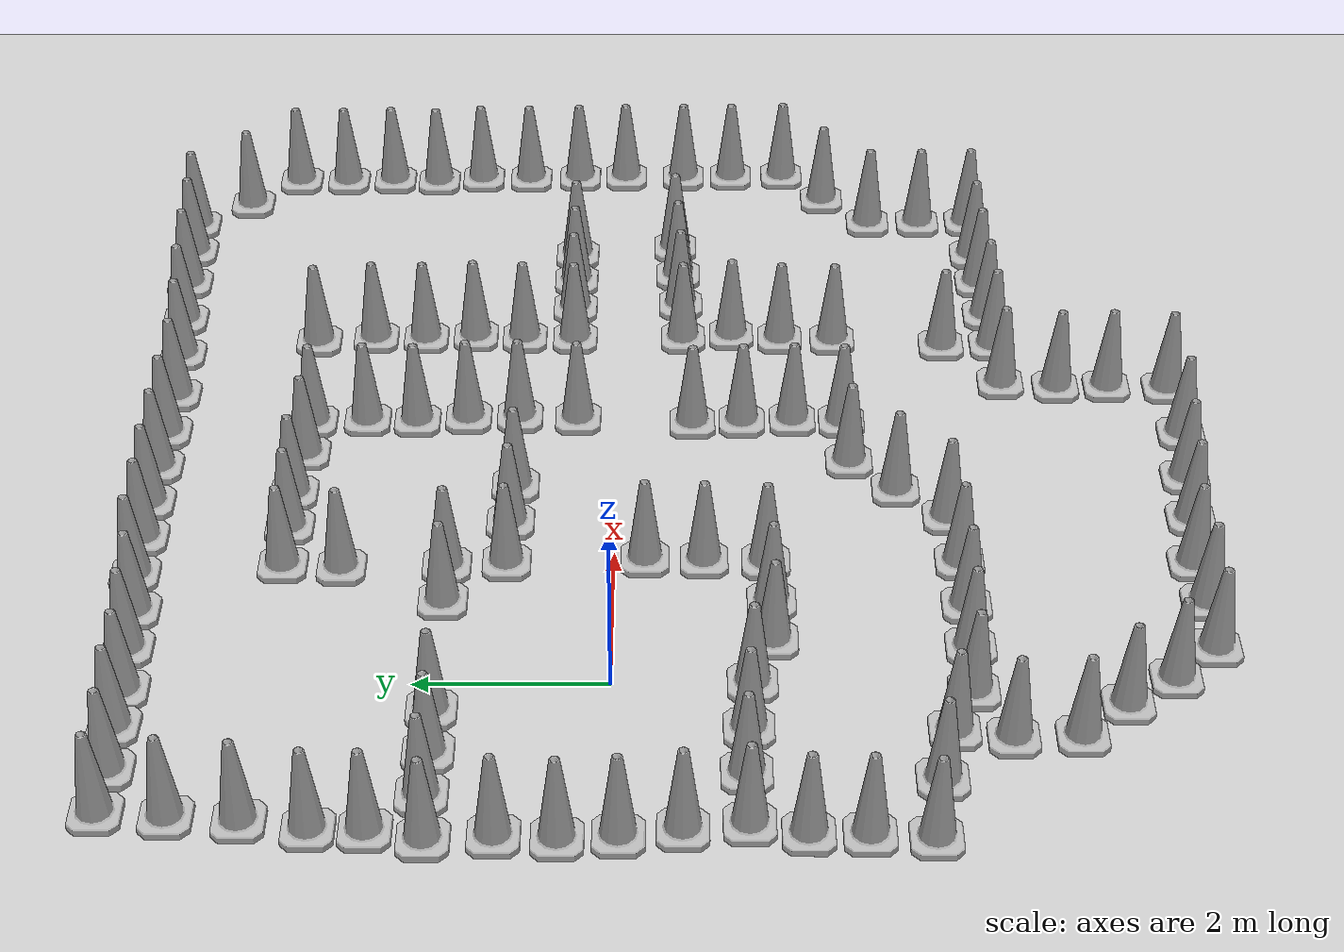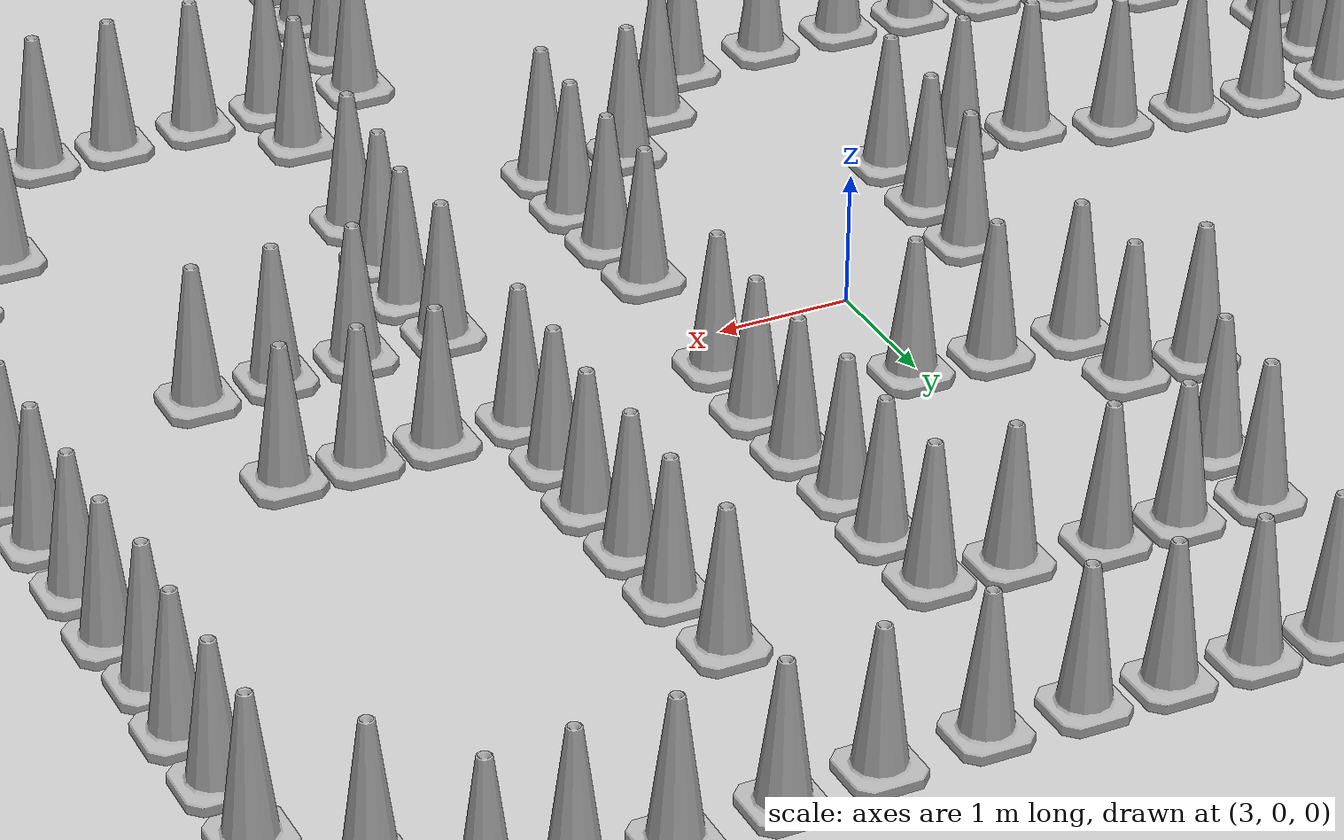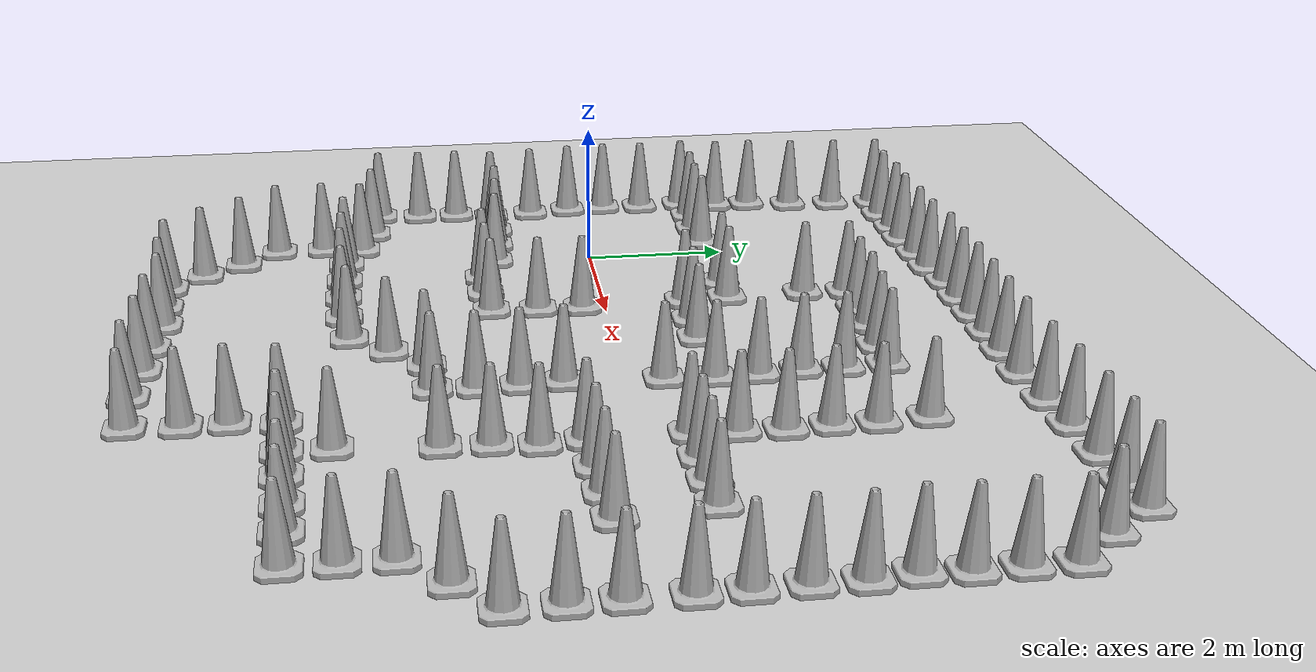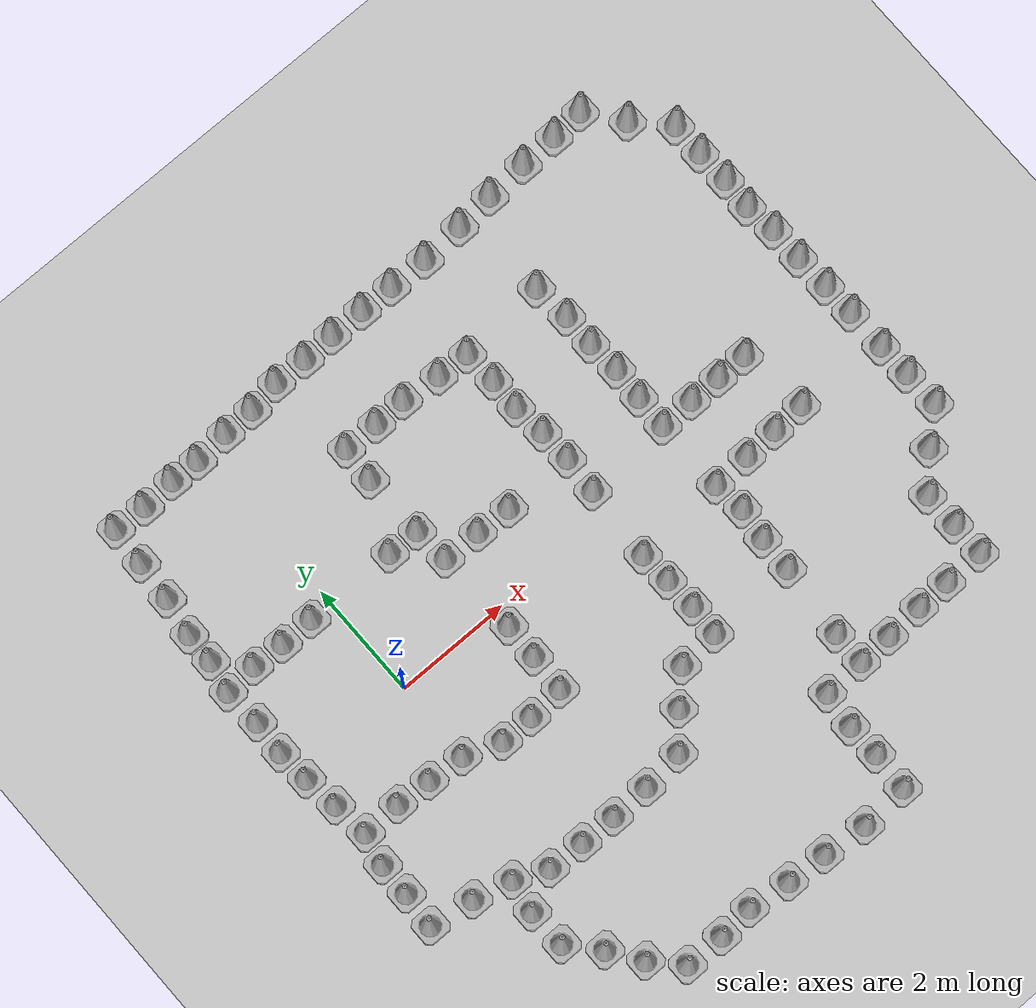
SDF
<sdf version="1.7">
 <world name="default">
  <light name="sun" type="directional">
   <pose>0 0 10 0 -0 0</pose>
   <diffuse>0.8 0.8 0.8 1</diffuse>
   <specular>0.2 0.2 0.2 1</specular>
   <attenuation>
    <range>1000</range>
    <constant>0.9</constant>
    <linear>0.01</linear>
    <quadratic>0.001</quadratic>
   </attenuation>
   <direction>-0.5 0.1 -0.9</direction>
   <spot><inner_angle>0</inner_angle><outer_angle>0</outer_angle><falloff>0</falloff></spot>
  </light>
  <model name="ground_plane">
   <static>1</static>
   <link name="link">
    <collision name="collision">
     <geometry><plane><normal>0 0 1</normal><size>100 100</size></plane></geometry>
     <surface>
      <contact><collide_bitmask>65535</collide_bitmask></contact>
      <friction><ode><mu>100</mu><mu2>50</mu2></ode></friction>
     </surface>
    </collision>
    <visual name="visual">
     <cast_shadows>0</cast_shadows>
     <geometry><plane><normal>0 0 1</normal><size>100 100</size></plane></geometry>
     <material>
      <script><uri>file://media/materials/scripts/gazebo.material</uri><name>Gazebo/Grey</name></script>
     </material>
    </visual>
   </link>
  </model>
  <gravity>0 0 -9.8</gravity>
  <magnetic_field>6e-06 2.3e-05 -4.2e-05</magnetic_field>
  <atmosphere type="adiabatic"/>
  <physics type="ode">
   <max_step_size>0.001</max_step_size>
   <real_time_factor>1</real_time_factor>
   <real_time_update_rate>1000</real_time_update_rate>
  </physics>
  <scene><ambient>0.4 0.4 0.4 1</ambient><background>0.7 0.7 0.7 1</background><shadows>1</shadows></scene>
  <spherical_coordinates>
   <surface_model>EARTH_WGS84</surface_model>
   <latitude_deg>0</latitude_deg>
   <longitude_deg>0</longitude_deg>
   <elevation>0</elevation>
   <heading_deg>0</heading_deg>
  </spherical_coordinates>
  <model name="Construction Cone">
   <link name="link">
    <collision name="collision">
     <geometry>
      <mesh><scale>10 10 10</scale><uri>model://construction_cone/meshes/construction_cone.dae</uri></mesh>
     </geometry>
    </collision>
    <visual name="visual">
     <geometry>
      <mesh><scale>10 10 10</scale><uri>model://construction_cone/meshes/construction_cone.dae</uri></mesh>
     </geometry>
    </visual>
    <inertial>
     <inertia><ixx>1</ixx><ixy>0</ixy><ixz>0</ixz><iyy>1</iyy><iyz>0</iyz><izz>1</izz></inertia>
     <mass>1</mass>
    </inertial>
   </link>
   <pose>-0.005243 -1.40875 -0 0 -1e-06 0</pose>
  </model>
  <model name="Construction Cone_0">
   <link name="link">
    <collision name="collision">
     <geometry>
      <mesh><scale>10 10 10</scale><uri>model://construction_cone/meshes/construction_cone.dae</uri></mesh>
     </geometry>
    </collision>
    <visual name="visual">
     <geometry>
      <mesh><scale>10 10 10</scale><uri>model://construction_cone/meshes/construction_cone.dae</uri></mesh>
     </geometry>
    </visual>
    <inertial>
     <inertia><ixx>1</ixx><ixy>0</ixy><ixz>0</ixz><iyy>1</iyy><iyz>0</iyz><izz>1</izz></inertia>
     <mass>1</mass>
    </inertial>
   </link>
   <pose>1.20298 -1.63455 -0 0 -1e-06 0</pose>
  </model>
  <model name="Construction Cone_1">
   <link name="link">
    <collision name="collision">
     <geometry>
      <mesh><scale>10 10 10</scale><uri>model://construction_cone/meshes/construction_cone.dae</uri></mesh>
     </geometry>
    </collision>
    <visual name="visual">
     <geometry>
      <mesh><scale>10 10 10</scale><uri>model://construction_cone/meshes/construction_cone.dae</uri></mesh>
     </geometry>
    </visual>
    <inertial>
     <inertia><ixx>1</ixx><ixy>0</ixy><ixz>0</ixz><iyy>1</iyy><iyz>0</iyz><izz>1</izz></inertia>
     <mass>1</mass>
    </inertial>
   </link>
   <pose>1.82506 -1.59296 -0 0 -0 0</pose>
  </model>
  <model name="Construction Cone_2">
   <link name="link">
    <collision name="collision">
     <geometry>
      <mesh><scale>10 10 10</scale><uri>model://construction_cone/meshes/construction_cone.dae</uri></mesh>
     </geometry>
    </collision>
    <visual name="visual">
     <geometry>
      <mesh><scale>10 10 10</scale><uri>model://construction_cone/meshes/construction_cone.dae</uri></mesh>
     </geometry>
    </visual>
    <inertial>
     <inertia><ixx>1</ixx><ixy>0</ixy><ixz>0</ixz><iyy>1</iyy><iyz>0</iyz><izz>1</izz></inertia>
     <mass>1</mass>
    </inertial>
   </link>
   <pose>0.620982 -1.63538 -0 0 -0 0</pose>
  </model>
  <model name="Construction Cone_3">
   <link name="link">
    <collision name="collision">
     <geometry>
      <mesh><scale>10 10 10</scale><uri>model://construction_cone/meshes/construction_cone.dae</uri></mesh>
     </geometry>
    </collision>
    <visual name="visual">
     <geometry>
      <mesh><scale>10 10 10</scale><uri>model://construction_cone/meshes/construction_cone.dae</uri></mesh>
     </geometry>
    </visual>
    <inertial>
     <inertia><ixx>1</ixx><ixy>0</ixy><ixz>0</ixz><iyy>1</iyy><iyz>0</iyz><izz>1</izz></inertia>
     <mass>1</mass>
    </inertial>
   </link>
   <pose>-0.64154 -1.35793 -0 0 -1e-06 0</pose>
  </model>
  <model name="Construction Cone_4">
   <link name="link">
    <collision name="collision">
     <geometry>
      <mesh><scale>10 10 10</scale><uri>model://construction_cone/meshes/construction_cone.dae</uri></mesh>
     </geometry>
    </collision>
    <visual name="visual">
     <geometry>
      <mesh><scale>10 10 10</scale><uri>model://construction_cone/meshes/construction_cone.dae</uri></mesh>
     </geometry>
    </visual>
    <inertial>
     <inertia><ixx>1</ixx><ixy>0</ixy><ixz>0</ixz><iyy>1</iyy><iyz>0</iyz><izz>1</izz></inertia>
     <mass>1</mass>
    </inertial>
   </link>
   <pose>-1.24859 -1.32205 -0 0 -0 0</pose>
  </model>
  <model name="Construction Cone_5">
   <link name="link">
    <collision name="collision">
     <geometry>
      <mesh><scale>10 10 10</scale><uri>model://construction_cone/meshes/construction_cone.dae</uri></mesh>
     </geometry>
    </collision>
    <visual name="visual">
     <geometry>
      <mesh><scale>10 10 10</scale><uri>model://construction_cone/meshes/construction_cone.dae</uri></mesh>
     </geometry>
    </visual>
    <inertial>
     <inertia><ixx>1</ixx><ixy>0</ixy><ixz>0</ixz><iyy>1</iyy><iyz>0</iyz><izz>1</izz></inertia>
     <mass>1</mass>
    </inertial>
   </link>
   <pose>-1.91656 -1.33623 -0 -0 -0 -0</pose>
  </model>
  <model name="Construction Cone_6">
   <link name="link">
    <collision name="collision">
     <geometry>
      <mesh><scale>10 10 10</scale><uri>model://construction_cone/meshes/construction_cone.dae</uri></mesh>
     </geometry>
    </collision>
    <visual name="visual">
     <geometry>
      <mesh><scale>10 10 10</scale><uri>model://construction_cone/meshes/construction_cone.dae</uri></mesh>
     </geometry>
    </visual>
    <inertial>
     <inertia><ixx>1</ixx><ixy>0</ixy><ixz>0</ixz><iyy>1</iyy><iyz>0</iyz><izz>1</izz></inertia>
     <mass>1</mass>
    </inertial>
   </link>
   <pose>-1.98763 -0.706466 -0 0 -0 0</pose>
  </model>
  <model name="Construction Cone_7">
   <link name="link">
    <collision name="collision">
     <geometry>
      <mesh><scale>10 10 10</scale><uri>model://construction_cone/meshes/construction_cone.dae</uri></mesh>
     </geometry>
    </collision>
    <visual name="visual">
     <geometry>
      <mesh><scale>10 10 10</scale><uri>model://construction_cone/meshes/construction_cone.dae</uri></mesh>
     </geometry>
    </visual>
    <inertial>
     <inertia><ixx>1</ixx><ixy>0</ixy><ixz>0</ixz><iyy>1</iyy><iyz>0</iyz><izz>1</izz></inertia>
     <mass>1</mass>
    </inertial>
   </link>
   <pose>-2.06657 -0.099365 -0 0 -0 0</pose>
  </model>
  <model name="Construction Cone_8">
   <link name="link">
    <collision name="collision">
     <geometry>
      <mesh><scale>10 10 10</scale><uri>model://construction_cone/meshes/construction_cone.dae</uri></mesh>
     </geometry>
    </collision>
    <visual name="visual">
     <geometry>
      <mesh><scale>10 10 10</scale><uri>model://construction_cone/meshes/construction_cone.dae</uri></mesh>
     </geometry>
    </visual>
    <inertial>
     <inertia><ixx>1</ixx><ixy>0</ixy><ixz>0</ixz><iyy>1</iyy><iyz>0</iyz><izz>1</izz></inertia>
     <mass>1</mass>
    </inertial>
   </link>
   <pose>-2.10442 0.47385 -0 0 -0 0</pose>
  </model>
  <model name="Construction Cone_9">
   <link name="link">
    <collision name="collision">
     <geometry>
      <mesh><scale>10 10 10</scale><uri>model://construction_cone/meshes/construction_cone.dae</uri></mesh>
     </geometry>
    </collision>
    <visual name="visual">
     <geometry>
      <mesh><scale>10 10 10</scale><uri>model://construction_cone/meshes/construction_cone.dae</uri></mesh>
     </geometry>
    </visual>
    <inertial>
     <inertia><ixx>1</ixx><ixy>0</ixy><ixz>0</ixz><iyy>1</iyy><iyz>0</iyz><izz>1</izz></inertia>
     <mass>1</mass>
    </inertial>
   </link>
   <pose>-2.07021 1.07184 -0 0 -0 0</pose>
  </model>
  <model name="Construction Cone_10">
   <link name="link">
    <collision name="collision">
     <geometry>
      <mesh><scale>10 10 10</scale><uri>model://construction_cone/meshes/construction_cone.dae</uri></mesh>
     </geometry>
    </collision>
    <visual name="visual">
     <geometry>
      <mesh><scale>10 10 10</scale><uri>model://construction_cone/meshes/construction_cone.dae</uri></mesh>
     </geometry>
    </visual>
    <inertial>
     <inertia><ixx>1</ixx><ixy>0</ixy><ixz>0</ixz><iyy>1</iyy><iyz>0</iyz><izz>1</izz></inertia>
     <mass>1</mass>
    </inertial>
   </link>
   <pose>1.85068 -0.9436 -0 0 -0 0</pose>
  </model>
  <model name="Construction Cone_11">
   <link name="link">
    <collision name="collision">
     <geometry>
      <mesh><scale>10 10 10</scale><uri>model://construction_cone/meshes/construction_cone.dae</uri></mesh>
     </geometry>
    </collision>
    <visual name="visual">
     <geometry>
      <mesh><scale>10 10 10</scale><uri>model://construction_cone/meshes/construction_cone.dae</uri></mesh>
     </geometry>
    </visual>
    <inertial>
     <inertia><ixx>1</ixx><ixy>0</ixy><ixz>0</ixz><iyy>1</iyy><iyz>0</iyz><izz>1</izz></inertia>
     <mass>1</mass>
    </inertial>
   </link>
   <pose>1.8693 -0.324364 -0 0 -0 0</pose>
  </model>
  <model name="Construction Cone_12">
   <link name="link">
    <collision name="collision">
     <geometry>
      <mesh><scale>10 10 10</scale><uri>model://construction_cone/meshes/construction_cone.dae</uri></mesh>
     </geometry>
    </collision>
    <visual name="visual">
     <geometry>
      <mesh><scale>10 10 10</scale><uri>model://construction_cone/meshes/construction_cone.dae</uri></mesh>
     </geometry>
    </visual>
    <inertial>
     <inertia><ixx>1</ixx><ixy>0</ixy><ixz>0</ixz><iyy>1</iyy><iyz>0</iyz><izz>1</izz></inertia>
     <mass>1</mass>
    </inertial>
   </link>
   <pose>-2.11151 1.73001 0 -0 -0 -0</pose>
  </model>
  <model name="Construction Cone_13">
   <link name="link">
    <collision name="collision">
     <geometry>
      <mesh><scale>10 10 10</scale><uri>model://construction_cone/meshes/construction_cone.dae</uri></mesh>
     </geometry>
    </collision>
    <visual name="visual">
     <geometry>
      <mesh><scale>10 10 10</scale><uri>model://construction_cone/meshes/construction_cone.dae</uri></mesh>
     </geometry>
    </visual>
    <inertial>
     <inertia><ixx>1</ixx><ixy>0</ixy><ixz>0</ixz><iyy>1</iyy><iyz>0</iyz><izz>1</izz></inertia>
     <mass>1</mass>
    </inertial>
   </link>
   <pose>-1.53957 1.78306 -0 0 -0 0</pose>
  </model>
  <model name="Construction Cone_14">
   <link name="link">
    <collision name="collision">
     <geometry>
      <mesh><scale>10 10 10</scale><uri>model://construction_cone/meshes/construction_cone.dae</uri></mesh>
     </geometry>
    </collision>
    <visual name="visual">
     <geometry>
      <mesh><scale>10 10 10</scale><uri>model://construction_cone/meshes/construction_cone.dae</uri></mesh>
     </geometry>
    </visual>
    <inertial>
     <inertia><ixx>1</ixx><ixy>0</ixy><ixz>0</ixz><iyy>1</iyy><iyz>0</iyz><izz>1</izz></inertia>
     <mass>1</mass>
    </inertial>
   </link>
   <pose>-0.975728 1.76072 -0 0 -0 0</pose>
  </model>
  <model name="Construction Cone_15">
   <link name="link">
    <collision name="collision">
     <geometry>
      <mesh><scale>10 10 10</scale><uri>model://construction_cone/meshes/construction_cone.dae</uri></mesh>
     </geometry>
    </collision>
    <visual name="visual">
     <geometry>
      <mesh><scale>10 10 10</scale><uri>model://construction_cone/meshes/construction_cone.dae</uri></mesh>
     </geometry>
    </visual>
    <inertial>
     <inertia><ixx>1</ixx><ixy>0</ixy><ixz>0</ixz><iyy>1</iyy><iyz>0</iyz><izz>1</izz></inertia>
     <mass>1</mass>
    </inertial>
   </link>
   <pose>-0.387008 1.76867 -0 0 -0 0</pose>
  </model>
  <model name="Construction Cone_16">
   <link name="link">
    <collision name="collision">
     <geometry>
      <mesh><scale>10 10 10</scale><uri>model://construction_cone/meshes/construction_cone.dae</uri></mesh>
     </geometry>
    </collision>
    <visual name="visual">
     <geometry>
      <mesh><scale>10 10 10</scale><uri>model://construction_cone/meshes/construction_cone.dae</uri></mesh>
     </geometry>
    </visual>
    <inertial>
     <inertia><ixx>1</ixx><ixy>0</ixy><ixz>0</ixz><iyy>1</iyy><iyz>0</iyz><izz>1</izz></inertia>
     <mass>1</mass>
    </inertial>
   </link>
   <pose>1.81349 1.12938 -0 0 -0 0</pose>
  </model>
  <model name="Construction Cone_17">
   <link name="link">
    <collision name="collision">
     <geometry>
      <mesh><scale>10 10 10</scale><uri>model://construction_cone/meshes/construction_cone.dae</uri></mesh>
     </geometry>
    </collision>
    <visual name="visual">
     <geometry>
      <mesh><scale>10 10 10</scale><uri>model://construction_cone/meshes/construction_cone.dae</uri></mesh>
     </geometry>
    </visual>
    <inertial>
     <inertia><ixx>1</ixx><ixy>0</ixy><ixz>0</ixz><iyy>1</iyy><iyz>0</iyz><izz>1</izz></inertia>
     <mass>1</mass>
    </inertial>
   </link>
   <pose>1.76686 1.75482 -0 0 -0 0</pose>
  </model>
  <model name="Construction Cone_18">
   <link name="link">
    <collision name="collision">
     <geometry>
      <mesh><scale>10 10 10</scale><uri>model://construction_cone/meshes/construction_cone.dae</uri></mesh>
     </geometry>
    </collision>
    <visual name="visual">
     <geometry>
      <mesh><scale>10 10 10</scale><uri>model://construction_cone/meshes/construction_cone.dae</uri></mesh>
     </geometry>
    </visual>
    <inertial>
     <inertia><ixx>1</ixx><ixy>0</ixy><ixz>0</ixz><iyy>1</iyy><iyz>0</iyz><izz>1</izz></inertia>
     <mass>1</mass>
    </inertial>
   </link>
   <pose>1.20932 1.76099 -0 0 -0 0</pose>
  </model>
  <model name="Construction Cone_19">
   <link name="link">
    <collision name="collision">
     <geometry>
      <mesh><scale>10 10 10</scale><uri>model://construction_cone/meshes/construction_cone.dae</uri></mesh>
     </geometry>
    </collision>
    <visual name="visual">
     <geometry>
      <mesh><scale>10 10 10</scale><uri>model://construction_cone/meshes/construction_cone.dae</uri></mesh>
     </geometry>
    </visual>
    <inertial>
     <inertia><ixx>1</ixx><ixy>0</ixy><ixz>0</ixz><iyy>1</iyy><iyz>0</iyz><izz>1</izz></inertia>
     <mass>1</mass>
    </inertial>
   </link>
   <pose>2.47039 1.11818 -0 -0 -0 -0</pose>
  </model>
  <model name="Construction Cone_20">
   <link name="link">
    <collision name="collision">
     <geometry>
      <mesh><scale>10 10 10</scale><uri>model://construction_cone/meshes/construction_cone.dae</uri></mesh>
     </geometry>
    </collision>
    <visual name="visual">
     <geometry>
      <mesh><scale>10 10 10</scale><uri>model://construction_cone/meshes/construction_cone.dae</uri></mesh>
     </geometry>
    </visual>
    <inertial>
     <inertia><ixx>1</ixx><ixy>0</ixy><ixz>0</ixz><iyy>1</iyy><iyz>0</iyz><izz>1</izz></inertia>
     <mass>1</mass>
    </inertial>
   </link>
   <pose>3.08287 1.09 -0 0 -0 0</pose>
  </model>
  <model name="Construction Cone_21">
   <link name="link">
    <collision name="collision">
     <geometry>
      <mesh><scale>10 10 10</scale><uri>model://construction_cone/meshes/construction_cone.dae</uri></mesh>
     </geometry>
    </collision>
    <visual name="visual">
     <geometry>
      <mesh><scale>10 10 10</scale><uri>model://construction_cone/meshes/construction_cone.dae</uri></mesh>
     </geometry>
    </visual>
    <inertial>
     <inertia><ixx>1</ixx><ixy>0</ixy><ixz>0</ixz><iyy>1</iyy><iyz>0</iyz><izz>1</izz></inertia>
     <mass>1</mass>
    </inertial>
   </link>
   <pose>4.29676 1.09476 -0 0 -0 0</pose>
  </model>
  <model name="Construction Cone_22">
   <link name="link">
    <collision name="collision">
     <geometry>
      <mesh><scale>10 10 10</scale><uri>model://construction_cone/meshes/construction_cone.dae</uri></mesh>
     </geometry>
    </collision>
    <visual name="visual">
     <geometry>
      <mesh><scale>10 10 10</scale><uri>model://construction_cone/meshes/construction_cone.dae</uri></mesh>
     </geometry>
    </visual>
    <inertial>
     <inertia><ixx>1</ixx><ixy>0</ixy><ixz>0</ixz><iyy>1</iyy><iyz>0</iyz><izz>1</izz></inertia>
     <mass>1</mass>
    </inertial>
   </link>
   <pose>4.27915 1.66864 -0 0 -0 0</pose>
  </model>
  <model name="Construction Cone_23">
   <link name="link">
    <collision name="collision">
     <geometry>
      <mesh><scale>10 10 10</scale><uri>model://construction_cone/meshes/construction_cone.dae</uri></mesh>
     </geometry>
    </collision>
    <visual name="visual">
     <geometry>
      <mesh><scale>10 10 10</scale><uri>model://construction_cone/meshes/construction_cone.dae</uri></mesh>
     </geometry>
    </visual>
    <inertial>
     <inertia><ixx>1</ixx><ixy>0</ixy><ixz>0</ixz><iyy>1</iyy><iyz>0</iyz><izz>1</izz></inertia>
     <mass>1</mass>
    </inertial>
   </link>
   <pose>4.22013 2.24031 -0 0 -0 0</pose>
  </model>
  <model name="Construction Cone_24">
   <link name="link">
    <collision name="collision">
     <geometry>
      <mesh><scale>10 10 10</scale><uri>model://construction_cone/meshes/construction_cone.dae</uri></mesh>
     </geometry>
    </collision>
    <visual name="visual">
     <geometry>
      <mesh><scale>10 10 10</scale><uri>model://construction_cone/meshes/construction_cone.dae</uri></mesh>
     </geometry>
    </visual>
    <inertial>
     <inertia><ixx>1</ixx><ixy>0</ixy><ixz>0</ixz><iyy>1</iyy><iyz>0</iyz><izz>1</izz></inertia>
     <mass>1</mass>
    </inertial>
   </link>
   <pose>4.23444 2.79979 0 -0 -0 -0</pose>
  </model>
  <model name="Construction Cone_25">
   <link name="link">
    <collision name="collision">
     <geometry>
      <mesh><scale>10 10 10</scale><uri>model://construction_cone/meshes/construction_cone.dae</uri></mesh>
     </geometry>
    </collision>
    <visual name="visual">
     <geometry>
      <mesh><scale>10 10 10</scale><uri>model://construction_cone/meshes/construction_cone.dae</uri></mesh>
     </geometry>
    </visual>
    <inertial>
     <inertia><ixx>1</ixx><ixy>0</ixy><ixz>0</ixz><iyy>1</iyy><iyz>0</iyz><izz>1</izz></inertia>
     <mass>1</mass>
    </inertial>
   </link>
   <pose>4.2051 3.39511 -0 0 -0 0</pose>
  </model>
  <model name="Construction Cone_26">
   <link name="link">
    <collision name="collision">
     <geometry>
      <mesh><scale>10 10 10</scale><uri>model://construction_cone/meshes/construction_cone.dae</uri></mesh>
     </geometry>
    </collision>
    <visual name="visual">
     <geometry>
      <mesh><scale>10 10 10</scale><uri>model://construction_cone/meshes/construction_cone.dae</uri></mesh>
     </geometry>
    </visual>
    <inertial>
     <inertia><ixx>1</ixx><ixy>0</ixy><ixz>0</ixz><iyy>1</iyy><iyz>0</iyz><izz>1</izz></inertia>
     <mass>1</mass>
    </inertial>
   </link>
   <pose>3.63468 3.42342 -0 0 -0 0</pose>
  </model>
  <model name="Construction Cone_27">
   <link name="link">
    <collision name="collision">
     <geometry>
      <mesh><scale>10 10 10</scale><uri>model://construction_cone/meshes/construction_cone.dae</uri></mesh>
     </geometry>
    </collision>
    <visual name="visual">
     <geometry>
      <mesh><scale>10 10 10</scale><uri>model://construction_cone/meshes/construction_cone.dae</uri></mesh>
     </geometry>
    </visual>
    <inertial>
     <inertia><ixx>1</ixx><ixy>0</ixy><ixz>0</ixz><iyy>1</iyy><iyz>0</iyz><izz>1</izz></inertia>
     <mass>1</mass>
    </inertial>
   </link>
   <pose>2.95527 3.48574 -0 0 -0 0</pose>
  </model>
  <model name="Construction Cone_28">
   <link name="link">
    <collision name="collision">
     <geometry>
      <mesh><scale>10 10 10</scale><uri>model://construction_cone/meshes/construction_cone.dae</uri></mesh>
     </geometry>
    </collision>
    <visual name="visual">
     <geometry>
      <mesh><scale>10 10 10</scale><uri>model://construction_cone/meshes/construction_cone.dae</uri></mesh>
     </geometry>
    </visual>
    <inertial>
     <inertia><ixx>1</ixx><ixy>0</ixy><ixz>0</ixz><iyy>1</iyy><iyz>0</iyz><izz>1</izz></inertia>
     <mass>1</mass>
    </inertial>
   </link>
   <pose>2.39059 3.47145 -0 0 -0 0</pose>
  </model>
  <model name="Construction Cone_29">
   <link name="link">
    <collision name="collision">
     <geometry>
      <mesh><scale>10 10 10</scale><uri>model://construction_cone/meshes/construction_cone.dae</uri></mesh>
     </geometry>
    </collision>
    <visual name="visual">
     <geometry>
      <mesh><scale>10 10 10</scale><uri>model://construction_cone/meshes/construction_cone.dae</uri></mesh>
     </geometry>
    </visual>
    <inertial>
     <inertia><ixx>1</ixx><ixy>0</ixy><ixz>0</ixz><iyy>1</iyy><iyz>0</iyz><izz>1</izz></inertia>
     <mass>1</mass>
    </inertial>
   </link>
   <pose>1.77181 3.47564 -0 0 -0 0</pose>
  </model>
  <model name="Construction Cone_30">
   <link name="link">
    <collision name="collision">
     <geometry>
      <mesh><scale>10 10 10</scale><uri>model://construction_cone/meshes/construction_cone.dae</uri></mesh>
     </geometry>
    </collision>
    <visual name="visual">
     <geometry>
      <mesh><scale>10 10 10</scale><uri>model://construction_cone/meshes/construction_cone.dae</uri></mesh>
     </geometry>
    </visual>
    <inertial>
     <inertia><ixx>1</ixx><ixy>0</ixy><ixz>0</ixz><iyy>1</iyy><iyz>0</iyz><izz>1</izz></inertia>
     <mass>1</mass>
    </inertial>
   </link>
   <pose>1.73716 2.85691 -0 0 -0 0</pose>
  </model>
  <model name="Construction Cone_31">
   <link name="link">
    <collision name="collision">
     <geometry>
      <mesh><scale>10 10 10</scale><uri>model://construction_cone/meshes/construction_cone.dae</uri></mesh>
     </geometry>
    </collision>
    <visual name="visual">
     <geometry>
      <mesh><scale>10 10 10</scale><uri>model://construction_cone/meshes/construction_cone.dae</uri></mesh>
     </geometry>
    </visual>
    <inertial>
     <inertia><ixx>1</ixx><ixy>0</ixy><ixz>0</ixz><iyy>1</iyy><iyz>0</iyz><izz>1</izz></inertia>
     <mass>1</mass>
    </inertial>
   </link>
   <pose>4.25954 0.441284 -0 0 -0 0</pose>
  </model>
  <model name="Construction Cone_32">
   <link name="link">
    <collision name="collision">
     <geometry>
      <mesh><scale>10 10 10</scale><uri>model://construction_cone/meshes/construction_cone.dae</uri></mesh>
     </geometry>
    </collision>
    <visual name="visual">
     <geometry>
      <mesh><scale>10 10 10</scale><uri>model://construction_cone/meshes/construction_cone.dae</uri></mesh>
     </geometry>
    </visual>
    <inertial>
     <inertia><ixx>1</ixx><ixy>0</ixy><ixz>0</ixz><iyy>1</iyy><iyz>0</iyz><izz>1</izz></inertia>
     <mass>1</mass>
    </inertial>
   </link>
   <pose>4.18784 -0.837495 -0 0 -0 0</pose>
  </model>
  <model name="Construction Cone_33">
   <link name="link">
    <collision name="collision">
     <geometry>
      <mesh><scale>10 10 10</scale><uri>model://construction_cone/meshes/construction_cone.dae</uri></mesh>
     </geometry>
    </collision>
    <visual name="visual">
     <geometry>
      <mesh><scale>10 10 10</scale><uri>model://construction_cone/meshes/construction_cone.dae</uri></mesh>
     </geometry>
    </visual>
    <inertial>
     <inertia><ixx>1</ixx><ixy>0</ixy><ixz>0</ixz><iyy>1</iyy><iyz>0</iyz><izz>1</izz></inertia>
     <mass>1</mass>
    </inertial>
   </link>
   <pose>4.21705 -1.39268 -0 0 -0 0</pose>
  </model>
  <model name="Construction Cone_34">
   <link name="link">
    <collision name="collision">
     <geometry>
      <mesh><scale>10 10 10</scale><uri>model://construction_cone/meshes/construction_cone.dae</uri></mesh>
     </geometry>
    </collision>
    <visual name="visual">
     <geometry>
      <mesh><scale>10 10 10</scale><uri>model://construction_cone/meshes/construction_cone.dae</uri></mesh>
     </geometry>
    </visual>
    <inertial>
     <inertia><ixx>1</ixx><ixy>0</ixy><ixz>0</ixz><iyy>1</iyy><iyz>0</iyz><izz>1</izz></inertia>
     <mass>1</mass>
    </inertial>
   </link>
   <pose>4.23931 -1.95743 -0 0 -0 0</pose>
  </model>
  <model name="Construction Cone_35">
   <link name="link">
    <collision name="collision">
     <geometry>
      <mesh><scale>10 10 10</scale><uri>model://construction_cone/meshes/construction_cone.dae</uri></mesh>
     </geometry>
    </collision>
    <visual name="visual">
     <geometry>
      <mesh><scale>10 10 10</scale><uri>model://construction_cone/meshes/construction_cone.dae</uri></mesh>
     </geometry>
    </visual>
    <inertial>
     <inertia><ixx>1</ixx><ixy>0</ixy><ixz>0</ixz><iyy>1</iyy><iyz>0</iyz><izz>1</izz></inertia>
     <mass>1</mass>
    </inertial>
   </link>
   <pose>4.21293 -2.50767 -0 0 -0 0</pose>
  </model>
  <model name="Construction Cone_36">
   <link name="link">
    <collision name="collision">
     <geometry>
      <mesh><scale>10 10 10</scale><uri>model://construction_cone/meshes/construction_cone.dae</uri></mesh>
     </geometry>
    </collision>
    <visual name="visual">
     <geometry>
      <mesh><scale>10 10 10</scale><uri>model://construction_cone/meshes/construction_cone.dae</uri></mesh>
     </geometry>
    </visual>
    <inertial>
     <inertia><ixx>1</ixx><ixy>0</ixy><ixz>0</ixz><iyy>1</iyy><iyz>0</iyz><izz>1</izz></inertia>
     <mass>1</mass>
    </inertial>
   </link>
   <pose>3.50327 -2.5545 -0 0 -0 0</pose>
  </model>
  <model name="Construction Cone_37">
   <link name="link">
    <collision name="collision">
     <geometry>
      <mesh><scale>10 10 10</scale><uri>model://construction_cone/meshes/construction_cone.dae</uri></mesh>
     </geometry>
    </collision>
    <visual name="visual">
     <geometry>
      <mesh><scale>10 10 10</scale><uri>model://construction_cone/meshes/construction_cone.dae</uri></mesh>
     </geometry>
    </visual>
    <inertial>
     <inertia><ixx>1</ixx><ixy>0</ixy><ixz>0</ixz><iyy>1</iyy><iyz>0</iyz><izz>1</izz></inertia>
     <mass>1</mass>
    </inertial>
   </link>
   <pose>3.01779 -3.03425 -0 0 -0 0</pose>
  </model>
  <model name="Construction Cone_38">
   <link name="link">
    <collision name="collision">
     <geometry>
      <mesh><scale>10 10 10</scale><uri>model://construction_cone/meshes/construction_cone.dae</uri></mesh>
     </geometry>
    </collision>
    <visual name="visual">
     <geometry>
      <mesh><scale>10 10 10</scale><uri>model://construction_cone/meshes/construction_cone.dae</uri></mesh>
     </geometry>
    </visual>
    <inertial>
     <inertia><ixx>1</ixx><ixy>0</ixy><ixz>0</ixz><iyy>1</iyy><iyz>0</iyz><izz>1</izz></inertia>
     <mass>1</mass>
    </inertial>
   </link>
   <pose>2.55423 -3.55356 -0 0 -0 0</pose>
  </model>
  <model name="Construction Cone_39">
   <link name="link">
    <collision name="collision">
     <geometry>
      <mesh><scale>10 10 10</scale><uri>model://construction_cone/meshes/construction_cone.dae</uri></mesh>
     </geometry>
    </collision>
    <visual name="visual">
     <geometry>
      <mesh><scale>10 10 10</scale><uri>model://construction_cone/meshes/construction_cone.dae</uri></mesh>
     </geometry>
    </visual>
    <inertial>
     <inertia><ixx>1</ixx><ixy>0</ixy><ixz>0</ixz><iyy>1</iyy><iyz>0</iyz><izz>1</izz></inertia>
     <mass>1</mass>
    </inertial>
   </link>
   <pose>1.8326 -3.62864 -0 0 -0 0</pose>
  </model>
  <model name="Construction Cone_40">
   <link name="link">
    <collision name="collision">
     <geometry>
      <mesh><scale>10 10 10</scale><uri>model://construction_cone/meshes/construction_cone.dae</uri></mesh>
     </geometry>
    </collision>
    <visual name="visual">
     <geometry>
      <mesh><scale>10 10 10</scale><uri>model://construction_cone/meshes/construction_cone.dae</uri></mesh>
     </geometry>
    </visual>
    <inertial>
     <inertia><ixx>1</ixx><ixy>0</ixy><ixz>0</ixz><iyy>1</iyy><iyz>0</iyz><izz>1</izz></inertia>
     <mass>1</mass>
    </inertial>
   </link>
   <pose>1.15052 -3.64418 -0 0 -0 0</pose>
  </model>
  <model name="Construction Cone_41">
   <link name="link">
    <collision name="collision">
     <geometry>
      <mesh><scale>10 10 10</scale><uri>model://construction_cone/meshes/construction_cone.dae</uri></mesh>
     </geometry>
    </collision>
    <visual name="visual">
     <geometry>
      <mesh><scale>10 10 10</scale><uri>model://construction_cone/meshes/construction_cone.dae</uri></mesh>
     </geometry>
    </visual>
    <inertial>
     <inertia><ixx>1</ixx><ixy>0</ixy><ixz>0</ixz><iyy>1</iyy><iyz>0</iyz><izz>1</izz></inertia>
     <mass>1</mass>
    </inertial>
   </link>
   <pose>0.522567 -3.63244 -0 0 -0 0</pose>
  </model>
  <model name="Construction Cone_42">
   <link name="link">
    <collision name="collision">
     <geometry>
      <mesh><scale>10 10 10</scale><uri>model://construction_cone/meshes/construction_cone.dae</uri></mesh>
     </geometry>
    </collision>
    <visual name="visual">
     <geometry>
      <mesh><scale>10 10 10</scale><uri>model://construction_cone/meshes/construction_cone.dae</uri></mesh>
     </geometry>
    </visual>
    <inertial>
     <inertia><ixx>1</ixx><ixy>0</ixy><ixz>0</ixz><iyy>1</iyy><iyz>0</iyz><izz>1</izz></inertia>
     <mass>1</mass>
    </inertial>
   </link>
   <pose>-0.11417 -3.60963 -0 0 -0 0</pose>
  </model>
  <model name="Construction Cone_43">
   <link name="link">
    <collision name="collision">
     <geometry>
      <mesh><scale>10 10 10</scale><uri>model://construction_cone/meshes/construction_cone.dae</uri></mesh>
     </geometry>
    </collision>
    <visual name="visual">
     <geometry>
      <mesh><scale>10 10 10</scale><uri>model://construction_cone/meshes/construction_cone.dae</uri></mesh>
     </geometry>
    </visual>
    <inertial>
     <inertia><ixx>1</ixx><ixy>0</ixy><ixz>0</ixz><iyy>1</iyy><iyz>0</iyz><izz>1</izz></inertia>
     <mass>1</mass>
    </inertial>
   </link>
   <pose>-0.6716 -3.36913 -0 0 -0 0</pose>
  </model>
  <model name="Construction Cone_44">
   <link name="link">
    <collision name="collision">
     <geometry>
      <mesh><scale>10 10 10</scale><uri>model://construction_cone/meshes/construction_cone.dae</uri></mesh>
     </geometry>
    </collision>
    <visual name="visual">
     <geometry>
      <mesh><scale>10 10 10</scale><uri>model://construction_cone/meshes/construction_cone.dae</uri></mesh>
     </geometry>
    </visual>
    <inertial>
     <inertia><ixx>1</ixx><ixy>0</ixy><ixz>0</ixz><iyy>1</iyy><iyz>0</iyz><izz>1</izz></inertia>
     <mass>1</mass>
    </inertial>
   </link>
   <pose>-1.32869 -3.20085 -0 0 -0 0</pose>
  </model>
  <model name="Construction Cone_45">
   <link name="link">
    <collision name="collision">
     <geometry>
      <mesh><scale>10 10 10</scale><uri>model://construction_cone/meshes/construction_cone.dae</uri></mesh>
     </geometry>
    </collision>
    <visual name="visual">
     <geometry>
      <mesh><scale>10 10 10</scale><uri>model://construction_cone/meshes/construction_cone.dae</uri></mesh>
     </geometry>
    </visual>
    <inertial>
     <inertia><ixx>1</ixx><ixy>0</ixy><ixz>0</ixz><iyy>1</iyy><iyz>0</iyz><izz>1</izz></inertia>
     <mass>1</mass>
    </inertial>
   </link>
   <pose>-2.0894 -3.0832 -0 0 -0 0</pose>
  </model>
  <model name="Construction Cone_46">
   <link name="link">
    <collision name="collision">
     <geometry>
      <mesh><scale>10 10 10</scale><uri>model://construction_cone/meshes/construction_cone.dae</uri></mesh>
     </geometry>
    </collision>
    <visual name="visual">
     <geometry>
      <mesh><scale>10 10 10</scale><uri>model://construction_cone/meshes/construction_cone.dae</uri></mesh>
     </geometry>
    </visual>
    <inertial>
     <inertia><ixx>1</ixx><ixy>0</ixy><ixz>0</ixz><iyy>1</iyy><iyz>0</iyz><izz>1</izz></inertia>
     <mass>1</mass>
    </inertial>
   </link>
   <pose>-2.04766 -2.46294 -0 0 -0 0</pose>
  </model>
  <model name="Construction Cone_47">
   <link name="link">
    <collision name="collision">
     <geometry>
      <mesh><scale>10 10 10</scale><uri>model://construction_cone/meshes/construction_cone.dae</uri></mesh>
     </geometry>
    </collision>
    <visual name="visual">
     <geometry>
      <mesh><scale>10 10 10</scale><uri>model://construction_cone/meshes/construction_cone.dae</uri></mesh>
     </geometry>
    </visual>
    <inertial>
     <inertia><ixx>1</ixx><ixy>0</ixy><ixz>0</ixz><iyy>1</iyy><iyz>0</iyz><izz>1</izz></inertia>
     <mass>1</mass>
    </inertial>
   </link>
   <pose>-2.03792 -1.88744 -0 0 -0 0</pose>
  </model>
  <model name="Construction Cone_48">
   <link name="link">
    <collision name="collision">
     <geometry>
      <mesh><scale>10 10 10</scale><uri>model://construction_cone/meshes/construction_cone.dae</uri></mesh>
     </geometry>
    </collision>
    <visual name="visual">
     <geometry>
      <mesh><scale>10 10 10</scale><uri>model://construction_cone/meshes/construction_cone.dae</uri></mesh>
     </geometry>
    </visual>
    <inertial>
     <inertia><ixx>1</ixx><ixy>0</ixy><ixz>0</ixz><iyy>1</iyy><iyz>0</iyz><izz>1</izz></inertia>
     <mass>1</mass>
    </inertial>
   </link>
   <pose>5.77529 0.514484 -0 0 -1e-06 0</pose>
  </model>
  <model name="Construction Cone_49">
   <link name="link">
    <collision name="collision">
     <geometry>
      <mesh><scale>10 10 10</scale><uri>model://construction_cone/meshes/construction_cone.dae</uri></mesh>
     </geometry>
    </collision>
    <visual name="visual">
     <geometry>
      <mesh><scale>10 10 10</scale><uri>model://construction_cone/meshes/construction_cone.dae</uri></mesh>
     </geometry>
    </visual>
    <inertial>
     <inertia><ixx>1</ixx><ixy>0</ixy><ixz>0</ixz><iyy>1</iyy><iyz>0</iyz><izz>1</izz></inertia>
     <mass>1</mass>
    </inertial>
   </link>
   <pose>5.78226 -0.740179 -0 0 -0 0</pose>
  </model>
  <model name="Construction Cone_50">
   <link name="link">
    <collision name="collision">
     <geometry>
      <mesh><scale>10 10 10</scale><uri>model://construction_cone/meshes/construction_cone.dae</uri></mesh>
     </geometry>
    </collision>
    <visual name="visual">
     <geometry>
      <mesh><scale>10 10 10</scale><uri>model://construction_cone/meshes/construction_cone.dae</uri></mesh>
     </geometry>
    </visual>
    <inertial>
     <inertia><ixx>1</ixx><ixy>0</ixy><ixz>0</ixz><iyy>1</iyy><iyz>0</iyz><izz>1</izz></inertia>
     <mass>1</mass>
    </inertial>
   </link>
   <pose>5.8438 -1.30153 -0 0 -1e-06 0</pose>
  </model>
  <model name="Construction Cone_51">
   <link name="link">
    <collision name="collision">
     <geometry>
      <mesh><scale>10 10 10</scale><uri>model://construction_cone/meshes/construction_cone.dae</uri></mesh>
     </geometry>
    </collision>
    <visual name="visual">
     <geometry>
      <mesh><scale>10 10 10</scale><uri>model://construction_cone/meshes/construction_cone.dae</uri></mesh>
     </geometry>
    </visual>
    <inertial>
     <inertia><ixx>1</ixx><ixy>0</ixy><ixz>0</ixz><iyy>1</iyy><iyz>0</iyz><izz>1</izz></inertia>
     <mass>1</mass>
    </inertial>
   </link>
   <pose>6.45008 -0.71454 -0 0 -1e-06 0</pose>
  </model>
  <model name="Construction Cone_52">
   <link name="link">
    <collision name="collision">
     <geometry>
      <mesh><scale>10 10 10</scale><uri>model://construction_cone/meshes/construction_cone.dae</uri></mesh>
     </geometry>
    </collision>
    <visual name="visual">
     <geometry>
      <mesh><scale>10 10 10</scale><uri>model://construction_cone/meshes/construction_cone.dae</uri></mesh>
     </geometry>
    </visual>
    <inertial>
     <inertia><ixx>1</ixx><ixy>0</ixy><ixz>0</ixz><iyy>1</iyy><iyz>0</iyz><izz>1</izz></inertia>
     <mass>1</mass>
    </inertial>
   </link>
   <pose>5.78905 1.10142 -0 0 -1e-06 0</pose>
  </model>
  <model name="Construction Cone_53">
   <link name="link">
    <collision name="collision">
     <geometry>
      <mesh><scale>10 10 10</scale><uri>model://construction_cone/meshes/construction_cone.dae</uri></mesh>
     </geometry>
    </collision>
    <visual name="visual">
     <geometry>
      <mesh><scale>10 10 10</scale><uri>model://construction_cone/meshes/construction_cone.dae</uri></mesh>
     </geometry>
    </visual>
    <inertial>
     <inertia><ixx>1</ixx><ixy>0</ixy><ixz>0</ixz><iyy>1</iyy><iyz>0</iyz><izz>1</izz></inertia>
     <mass>1</mass>
    </inertial>
   </link>
   <pose>6.38293 0.527132 -0 0 -0 0</pose>
  </model>
  <model name="Construction Cone_54">
   <link name="link">
    <collision name="collision">
     <geometry>
      <mesh><scale>10 10 10</scale><uri>model://construction_cone/meshes/construction_cone.dae</uri></mesh>
     </geometry>
    </collision>
    <visual name="visual">
     <geometry>
      <mesh><scale>10 10 10</scale><uri>model://construction_cone/meshes/construction_cone.dae</uri></mesh>
     </geometry>
    </visual>
    <inertial>
     <inertia><ixx>1</ixx><ixy>0</ixy><ixz>0</ixz><iyy>1</iyy><iyz>0</iyz><izz>1</izz></inertia>
     <mass>1</mass>
    </inertial>
   </link>
   <pose>7.05494 -0.687244 -0 0 -0 0</pose>
  </model>
  <model name="Construction Cone_55">
   <link name="link">
    <collision name="collision">
     <geometry>
      <mesh><scale>10 10 10</scale><uri>model://construction_cone/meshes/construction_cone.dae</uri></mesh>
     </geometry>
    </collision>
    <visual name="visual">
     <geometry>
      <mesh><scale>10 10 10</scale><uri>model://construction_cone/meshes/construction_cone.dae</uri></mesh>
     </geometry>
    </visual>
    <inertial>
     <inertia><ixx>1</ixx><ixy>0</ixy><ixz>0</ixz><iyy>1</iyy><iyz>0</iyz><izz>1</izz></inertia>
     <mass>1</mass>
    </inertial>
   </link>
   <pose>7.64263 -0.654383 -0 0 -0 0</pose>
  </model>
  <model name="Construction Cone_56">
   <link name="link">
    <collision name="collision">
     <geometry>
      <mesh><scale>10 10 10</scale><uri>model://construction_cone/meshes/construction_cone.dae</uri></mesh>
     </geometry>
    </collision>
    <visual name="visual">
     <geometry>
      <mesh><scale>10 10 10</scale><uri>model://construction_cone/meshes/construction_cone.dae</uri></mesh>
     </geometry>
    </visual>
    <inertial>
     <inertia><ixx>1</ixx><ixy>0</ixy><ixz>0</ixz><iyy>1</iyy><iyz>0</iyz><izz>1</izz></inertia>
     <mass>1</mass>
    </inertial>
   </link>
   <pose>5.77332 -1.86627 -0 0 -1e-06 0</pose>
  </model>
  <model name="Construction Cone_57">
   <link name="link">
    <collision name="collision">
     <geometry>
      <mesh><scale>10 10 10</scale><uri>model://construction_cone/meshes/construction_cone.dae</uri></mesh>
     </geometry>
    </collision>
    <visual name="visual">
     <geometry>
      <mesh><scale>10 10 10</scale><uri>model://construction_cone/meshes/construction_cone.dae</uri></mesh>
     </geometry>
    </visual>
    <inertial>
     <inertia><ixx>1</ixx><ixy>0</ixy><ixz>0</ixz><iyy>1</iyy><iyz>0</iyz><izz>1</izz></inertia>
     <mass>1</mass>
    </inertial>
   </link>
   <pose>5.75136 -2.47488 -0 0 -0 0</pose>
  </model>
  <model name="Construction Cone_58">
   <link name="link">
    <collision name="collision">
     <geometry>
      <mesh><scale>10 10 10</scale><uri>model://construction_cone/meshes/construction_cone.dae</uri></mesh>
     </geometry>
    </collision>
    <visual name="visual">
     <geometry>
      <mesh><scale>10 10 10</scale><uri>model://construction_cone/meshes/construction_cone.dae</uri></mesh>
     </geometry>
    </visual>
    <inertial>
     <inertia><ixx>1</ixx><ixy>0</ixy><ixz>0</ixz><iyy>1</iyy><iyz>0</iyz><izz>1</izz></inertia>
     <mass>1</mass>
    </inertial>
   </link>
   <pose>6.9423 0.529005 -0 0 -1e-06 0</pose>
  </model>
  <model name="Construction Cone_59">
   <link name="link">
    <collision name="collision">
     <geometry>
      <mesh><scale>10 10 10</scale><uri>model://construction_cone/meshes/construction_cone.dae</uri></mesh>
     </geometry>
    </collision>
    <visual name="visual">
     <geometry>
      <mesh><scale>10 10 10</scale><uri>model://construction_cone/meshes/construction_cone.dae</uri></mesh>
     </geometry>
    </visual>
    <inertial>
     <inertia><ixx>1</ixx><ixy>0</ixy><ixz>0</ixz><iyy>1</iyy><iyz>0</iyz><izz>1</izz></inertia>
     <mass>1</mass>
    </inertial>
   </link>
   <pose>7.48709 0.52778 -0 0 -1e-06 0</pose>
  </model>
  <model name="Construction Cone_60">
   <link name="link">
    <collision name="collision">
     <geometry>
      <mesh><scale>10 10 10</scale><uri>model://construction_cone/meshes/construction_cone.dae</uri></mesh>
     </geometry>
    </collision>
    <visual name="visual">
     <geometry>
      <mesh><scale>10 10 10</scale><uri>model://construction_cone/meshes/construction_cone.dae</uri></mesh>
     </geometry>
    </visual>
    <inertial>
     <inertia><ixx>1</ixx><ixy>0</ixy><ixz>0</ixz><iyy>1</iyy><iyz>0</iyz><izz>1</izz></inertia>
     <mass>1</mass>
    </inertial>
   </link>
   <pose>5.81809 1.67331 -0 0 -1e-06 0</pose>
  </model>
  <model name="Construction Cone_61">
   <link name="link">
    <collision name="collision">
     <geometry>
      <mesh><scale>10 10 10</scale><uri>model://construction_cone/meshes/construction_cone.dae</uri></mesh>
     </geometry>
    </collision>
    <visual name="visual">
     <geometry>
      <mesh><scale>10 10 10</scale><uri>model://construction_cone/meshes/construction_cone.dae</uri></mesh>
     </geometry>
    </visual>
    <inertial>
     <inertia><ixx>1</ixx><ixy>0</ixy><ixz>0</ixz><iyy>1</iyy><iyz>0</iyz><izz>1</izz></inertia>
     <mass>1</mass>
    </inertial>
   </link>
   <pose>5.78102 2.25076 -0 0 -0 0</pose>
  </model>
  <model name="Construction Cone_62">
   <link name="link">
    <collision name="collision">
     <geometry>
      <mesh><scale>10 10 10</scale><uri>model://construction_cone/meshes/construction_cone.dae</uri></mesh>
     </geometry>
    </collision>
    <visual name="visual">
     <geometry>
      <mesh><scale>10 10 10</scale><uri>model://construction_cone/meshes/construction_cone.dae</uri></mesh>
     </geometry>
    </visual>
    <inertial>
     <inertia><ixx>1</ixx><ixy>0</ixy><ixz>0</ixz><iyy>1</iyy><iyz>0</iyz><izz>1</izz></inertia>
     <mass>1</mass>
    </inertial>
   </link>
   <pose>5.78332 2.83354 -0 0 -0 0</pose>
  </model>
  <model name="Construction Cone_63">
   <link name="link">
    <collision name="collision">
     <geometry>
      <mesh><scale>10 10 10</scale><uri>model://construction_cone/meshes/construction_cone.dae</uri></mesh>
     </geometry>
    </collision>
    <visual name="visual">
     <geometry>
      <mesh><scale>10 10 10</scale><uri>model://construction_cone/meshes/construction_cone.dae</uri></mesh>
     </geometry>
    </visual>
    <inertial>
     <inertia><ixx>1</ixx><ixy>0</ixy><ixz>0</ixz><iyy>1</iyy><iyz>0</iyz><izz>1</izz></inertia>
     <mass>1</mass>
    </inertial>
   </link>
   <pose>5.72161 3.4937 -0 0 -1e-06 0</pose>
  </model>
  <model name="Construction Cone_64">
   <link name="link">
    <collision name="collision">
     <geometry>
      <mesh><scale>10 10 10</scale><uri>model://construction_cone/meshes/construction_cone.dae</uri></mesh>
     </geometry>
    </collision>
    <visual name="visual">
     <geometry>
      <mesh><scale>10 10 10</scale><uri>model://construction_cone/meshes/construction_cone.dae</uri></mesh>
     </geometry>
    </visual>
    <inertial>
     <inertia><ixx>1</ixx><ixy>0</ixy><ixz>0</ixz><iyy>1</iyy><iyz>0</iyz><izz>1</izz></inertia>
     <mass>1</mass>
    </inertial>
   </link>
   <pose>5.64487 -3.73638 -0 0 -1e-06 0</pose>
  </model>
  <model name="Construction Cone_65">
   <link name="link">
    <collision name="collision">
     <geometry>
      <mesh><scale>10 10 10</scale><uri>model://construction_cone/meshes/construction_cone.dae</uri></mesh>
     </geometry>
    </collision>
    <visual name="visual">
     <geometry>
      <mesh><scale>10 10 10</scale><uri>model://construction_cone/meshes/construction_cone.dae</uri></mesh>
     </geometry>
    </visual>
    <inertial>
     <inertia><ixx>1</ixx><ixy>0</ixy><ixz>0</ixz><iyy>1</iyy><iyz>0</iyz><izz>1</izz></inertia>
     <mass>1</mass>
    </inertial>
   </link>
   <pose>5.64718 -4.32758 -0 0 -0 0</pose>
  </model>
  <model name="Construction Cone_66">
   <link name="link">
    <collision name="collision">
     <geometry>
      <mesh><scale>10 10 10</scale><uri>model://construction_cone/meshes/construction_cone.dae</uri></mesh>
     </geometry>
    </collision>
    <visual name="visual">
     <geometry>
      <mesh><scale>10 10 10</scale><uri>model://construction_cone/meshes/construction_cone.dae</uri></mesh>
     </geometry>
    </visual>
    <inertial>
     <inertia><ixx>1</ixx><ixy>0</ixy><ixz>0</ixz><iyy>1</iyy><iyz>0</iyz><izz>1</izz></inertia>
     <mass>1</mass>
    </inertial>
   </link>
   <pose>6.24476 -4.30493 -0 0 -1e-06 0</pose>
  </model>
  <model name="Construction Cone_67">
   <link name="link">
    <collision name="collision">
     <geometry>
      <mesh><scale>10 10 10</scale><uri>model://construction_cone/meshes/construction_cone.dae</uri></mesh>
     </geometry>
    </collision>
    <visual name="visual">
     <geometry>
      <mesh><scale>10 10 10</scale><uri>model://construction_cone/meshes/construction_cone.dae</uri></mesh>
     </geometry>
    </visual>
    <inertial>
     <inertia><ixx>1</ixx><ixy>0</ixy><ixz>0</ixz><iyy>1</iyy><iyz>0</iyz><izz>1</izz></inertia>
     <mass>1</mass>
    </inertial>
   </link>
   <pose>6.90155 -4.27025 -0 0 -1e-06 0</pose>
  </model>
  <model name="Construction Cone_68">
   <link name="link">
    <collision name="collision">
     <geometry>
      <mesh><scale>10 10 10</scale><uri>model://construction_cone/meshes/construction_cone.dae</uri></mesh>
     </geometry>
    </collision>
    <visual name="visual">
     <geometry>
      <mesh><scale>10 10 10</scale><uri>model://construction_cone/meshes/construction_cone.dae</uri></mesh>
     </geometry>
    </visual>
    <inertial>
     <inertia><ixx>1</ixx><ixy>0</ixy><ixz>0</ixz><iyy>1</iyy><iyz>0</iyz><izz>1</izz></inertia>
     <mass>1</mass>
    </inertial>
   </link>
   <pose>7.48879 -4.25329 -0 0 -1e-06 0</pose>
  </model>
  <model name="Construction Cone_69">
   <link name="link">
    <collision name="collision">
     <geometry>
      <mesh><scale>10 10 10</scale><uri>model://construction_cone/meshes/construction_cone.dae</uri></mesh>
     </geometry>
    </collision>
    <visual name="visual">
     <geometry>
      <mesh><scale>10 10 10</scale><uri>model://construction_cone/meshes/construction_cone.dae</uri></mesh>
     </geometry>
    </visual>
    <inertial>
     <inertia><ixx>1</ixx><ixy>0</ixy><ixz>0</ixz><iyy>1</iyy><iyz>0</iyz><izz>1</izz></inertia>
     <mass>1</mass>
    </inertial>
   </link>
   <pose>8.19446 -4.24738 -0 0 -1e-06 0</pose>
  </model>
  <model name="Construction Cone_70">
   <link name="link">
    <collision name="collision">
     <geometry>
      <mesh><scale>10 10 10</scale><uri>model://construction_cone/meshes/construction_cone.dae</uri></mesh>
     </geometry>
    </collision>
    <visual name="visual">
     <geometry>
      <mesh><scale>10 10 10</scale><uri>model://construction_cone/meshes/construction_cone.dae</uri></mesh>
     </geometry>
    </visual>
    <inertial>
     <inertia><ixx>1</ixx><ixy>0</ixy><ixz>0</ixz><iyy>1</iyy><iyz>0</iyz><izz>1</izz></inertia>
     <mass>1</mass>
    </inertial>
   </link>
   <pose>8.18788 -3.64559 -0 0 -0 0</pose>
  </model>
  <model name="Construction Cone_71">
   <link name="link">
    <collision name="collision">
     <geometry>
      <mesh><scale>10 10 10</scale><uri>model://construction_cone/meshes/construction_cone.dae</uri></mesh>
     </geometry>
    </collision>
    <visual name="visual">
     <geometry>
      <mesh><scale>10 10 10</scale><uri>model://construction_cone/meshes/construction_cone.dae</uri></mesh>
     </geometry>
    </visual>
    <inertial>
     <inertia><ixx>1</ixx><ixy>0</ixy><ixz>0</ixz><iyy>1</iyy><iyz>0</iyz><izz>1</izz></inertia>
     <mass>1</mass>
    </inertial>
   </link>
   <pose>8.18697 -3.02915 -0 0 -1e-06 0</pose>
  </model>
  <model name="Construction Cone_72">
   <link name="link">
    <collision name="collision">
     <geometry>
      <mesh><scale>10 10 10</scale><uri>model://construction_cone/meshes/construction_cone.dae</uri></mesh>
     </geometry>
    </collision>
    <visual name="visual">
     <geometry>
      <mesh><scale>10 10 10</scale><uri>model://construction_cone/meshes/construction_cone.dae</uri></mesh>
     </geometry>
    </visual>
    <inertial>
     <inertia><ixx>1</ixx><ixy>0</ixy><ixz>0</ixz><iyy>1</iyy><iyz>0</iyz><izz>1</izz></inertia>
     <mass>1</mass>
    </inertial>
   </link>
   <pose>8.70114 -2.48312 -0 0 -0 0</pose>
  </model>
  <model name="Construction Cone_73">
   <link name="link">
    <collision name="collision">
     <geometry>
      <mesh><scale>10 10 10</scale><uri>model://construction_cone/meshes/construction_cone.dae</uri></mesh>
     </geometry>
    </collision>
    <visual name="visual">
     <geometry>
      <mesh><scale>10 10 10</scale><uri>model://construction_cone/meshes/construction_cone.dae</uri></mesh>
     </geometry>
    </visual>
    <inertial>
     <inertia><ixx>1</ixx><ixy>0</ixy><ixz>0</ixz><iyy>1</iyy><iyz>0</iyz><izz>1</izz></inertia>
     <mass>1</mass>
    </inertial>
   </link>
   <pose>9.24621 -1.9988 -0 0 -1e-06 0</pose>
  </model>
  <model name="Construction Cone_74">
   <link name="link">
    <collision name="collision">
     <geometry>
      <mesh><scale>10 10 10</scale><uri>model://construction_cone/meshes/construction_cone.dae</uri></mesh>
     </geometry>
    </collision>
    <visual name="visual">
     <geometry>
      <mesh><scale>10 10 10</scale><uri>model://construction_cone/meshes/construction_cone.dae</uri></mesh>
     </geometry>
    </visual>
    <inertial>
     <inertia><ixx>1</ixx><ixy>0</ixy><ixz>0</ixz><iyy>1</iyy><iyz>0</iyz><izz>1</izz></inertia>
     <mass>1</mass>
    </inertial>
   </link>
   <pose>9.23075 -1.35834 -0 0 -1e-06 0</pose>
  </model>
  <model name="Construction Cone_75">
   <link name="link">
    <collision name="collision">
     <geometry>
      <mesh><scale>10 10 10</scale><uri>model://construction_cone/meshes/construction_cone.dae</uri></mesh>
     </geometry>
    </collision>
    <visual name="visual">
     <geometry>
      <mesh><scale>10 10 10</scale><uri>model://construction_cone/meshes/construction_cone.dae</uri></mesh>
     </geometry>
    </visual>
    <inertial>
     <inertia><ixx>1</ixx><ixy>0</ixy><ixz>0</ixz><iyy>1</iyy><iyz>0</iyz><izz>1</izz></inertia>
     <mass>1</mass>
    </inertial>
   </link>
   <pose>9.22109 -0.762641 -0 0 -1e-06 0</pose>
  </model>
  <model name="Construction Cone_76">
   <link name="link">
    <collision name="collision">
     <geometry>
      <mesh><scale>10 10 10</scale><uri>model://construction_cone/meshes/construction_cone.dae</uri></mesh>
     </geometry>
    </collision>
    <visual name="visual">
     <geometry>
      <mesh><scale>10 10 10</scale><uri>model://construction_cone/meshes/construction_cone.dae</uri></mesh>
     </geometry>
    </visual>
    <inertial>
     <inertia><ixx>1</ixx><ixy>0</ixy><ixz>0</ixz><iyy>1</iyy><iyz>0</iyz><izz>1</izz></inertia>
     <mass>1</mass>
    </inertial>
   </link>
   <pose>9.22043 -0.040389 -0 0 -0 0</pose>
  </model>
  <model name="Construction Cone_77">
   <link name="link">
    <collision name="collision">
     <geometry>
      <mesh><scale>10 10 10</scale><uri>model://construction_cone/meshes/construction_cone.dae</uri></mesh>
     </geometry>
    </collision>
    <visual name="visual">
     <geometry>
      <mesh><scale>10 10 10</scale><uri>model://construction_cone/meshes/construction_cone.dae</uri></mesh>
     </geometry>
    </visual>
    <inertial>
     <inertia><ixx>1</ixx><ixy>0</ixy><ixz>0</ixz><iyy>1</iyy><iyz>0</iyz><izz>1</izz></inertia>
     <mass>1</mass>
    </inertial>
   </link>
   <pose>9.20167 0.540591 -0 0 -0 0</pose>
  </model>
  <model name="Construction Cone_78">
   <link name="link">
    <collision name="collision">
     <geometry>
      <mesh><scale>10 10 10</scale><uri>model://construction_cone/meshes/construction_cone.dae</uri></mesh>
     </geometry>
    </collision>
    <visual name="visual">
     <geometry>
      <mesh><scale>10 10 10</scale><uri>model://construction_cone/meshes/construction_cone.dae</uri></mesh>
     </geometry>
    </visual>
    <inertial>
     <inertia><ixx>1</ixx><ixy>0</ixy><ixz>0</ixz><iyy>1</iyy><iyz>0</iyz><izz>1</izz></inertia>
     <mass>1</mass>
    </inertial>
   </link>
   <pose>9.17944 1.16024 -0 0 -1e-06 0</pose>
  </model>
  <model name="Construction Cone_79">
   <link name="link">
    <collision name="collision">
     <geometry>
      <mesh><scale>10 10 10</scale><uri>model://construction_cone/meshes/construction_cone.dae</uri></mesh>
     </geometry>
    </collision>
    <visual name="visual">
     <geometry>
      <mesh><scale>10 10 10</scale><uri>model://construction_cone/meshes/construction_cone.dae</uri></mesh>
     </geometry>
    </visual>
    <inertial>
     <inertia><ixx>1</ixx><ixy>0</ixy><ixz>0</ixz><iyy>1</iyy><iyz>0</iyz><izz>1</izz></inertia>
     <mass>1</mass>
    </inertial>
   </link>
   <pose>9.18199 1.76212 -0 0 -1e-06 0</pose>
  </model>
  <model name="Construction Cone_80">
   <link name="link">
    <collision name="collision">
     <geometry>
      <mesh><scale>10 10 10</scale><uri>model://construction_cone/meshes/construction_cone.dae</uri></mesh>
     </geometry>
    </collision>
    <visual name="visual">
     <geometry>
      <mesh><scale>10 10 10</scale><uri>model://construction_cone/meshes/construction_cone.dae</uri></mesh>
     </geometry>
    </visual>
    <inertial>
     <inertia><ixx>1</ixx><ixy>0</ixy><ixz>0</ixz><iyy>1</iyy><iyz>0</iyz><izz>1</izz></inertia>
     <mass>1</mass>
    </inertial>
   </link>
   <pose>9.1166 2.31998 -0 0 -0 0</pose>
  </model>
  <model name="Construction Cone_81">
   <link name="link">
    <collision name="collision">
     <geometry>
      <mesh><scale>10 10 10</scale><uri>model://construction_cone/meshes/construction_cone.dae</uri></mesh>
     </geometry>
    </collision>
    <visual name="visual">
     <geometry>
      <mesh><scale>10 10 10</scale><uri>model://construction_cone/meshes/construction_cone.dae</uri></mesh>
     </geometry>
    </visual>
    <inertial>
     <inertia><ixx>1</ixx><ixy>0</ixy><ixz>0</ixz><iyy>1</iyy><iyz>0</iyz><izz>1</izz></inertia>
     <mass>1</mass>
    </inertial>
   </link>
   <pose>9.14789 2.87869 -0 0 -1e-06 0</pose>
  </model>
  <model name="Construction Cone_82">
   <link name="link">
    <collision name="collision">
     <geometry>
      <mesh><scale>10 10 10</scale><uri>model://construction_cone/meshes/construction_cone.dae</uri></mesh>
     </geometry>
    </collision>
    <visual name="visual">
     <geometry>
      <mesh><scale>10 10 10</scale><uri>model://construction_cone/meshes/construction_cone.dae</uri></mesh>
     </geometry>
    </visual>
    <inertial>
     <inertia><ixx>1</ixx><ixy>0</ixy><ixz>0</ixz><iyy>1</iyy><iyz>0</iyz><izz>1</izz></inertia>
     <mass>1</mass>
    </inertial>
   </link>
   <pose>9.12885 3.46501 -0 0 -1e-06 0</pose>
  </model>
  <model name="Construction Cone_83">
   <link name="link">
    <collision name="collision">
     <geometry>
      <mesh><scale>10 10 10</scale><uri>model://construction_cone/meshes/construction_cone.dae</uri></mesh>
     </geometry>
    </collision>
    <visual name="visual">
     <geometry>
      <mesh><scale>10 10 10</scale><uri>model://construction_cone/meshes/construction_cone.dae</uri></mesh>
     </geometry>
    </visual>
    <inertial>
     <inertia><ixx>1</ixx><ixy>0</ixy><ixz>0</ixz><iyy>1</iyy><iyz>0</iyz><izz>1</izz></inertia>
     <mass>1</mass>
    </inertial>
   </link>
   <pose>9.13226 4.05989 -0 0 -0 0</pose>
  </model>
  <model name="Construction Cone_84">
   <link name="link">
    <collision name="collision">
     <geometry>
      <mesh><scale>10 10 10</scale><uri>model://construction_cone/meshes/construction_cone.dae</uri></mesh>
     </geometry>
    </collision>
    <visual name="visual">
     <geometry>
      <mesh><scale>10 10 10</scale><uri>model://construction_cone/meshes/construction_cone.dae</uri></mesh>
     </geometry>
    </visual>
    <inertial>
     <inertia><ixx>1</ixx><ixy>0</ixy><ixz>0</ixz><iyy>1</iyy><iyz>0</iyz><izz>1</izz></inertia>
     <mass>1</mass>
    </inertial>
   </link>
   <pose>8.5995 4.61075 -0 0 -1e-06 0</pose>
  </model>
  <model name="Construction Cone_85">
   <link name="link">
    <collision name="collision">
     <geometry>
      <mesh><scale>10 10 10</scale><uri>model://construction_cone/meshes/construction_cone.dae</uri></mesh>
     </geometry>
    </collision>
    <visual name="visual">
     <geometry>
      <mesh><scale>10 10 10</scale><uri>model://construction_cone/meshes/construction_cone.dae</uri></mesh>
     </geometry>
    </visual>
    <inertial>
     <inertia><ixx>1</ixx><ixy>0</ixy><ixz>0</ixz><iyy>1</iyy><iyz>0</iyz><izz>1</izz></inertia>
     <mass>1</mass>
    </inertial>
   </link>
   <pose>8.13119 5.22336 -0 0 -1e-06 0</pose>
  </model>
  <model name="Construction Cone_86">
   <link name="link">
    <collision name="collision">
     <geometry>
      <mesh><scale>10 10 10</scale><uri>model://construction_cone/meshes/construction_cone.dae</uri></mesh>
     </geometry>
    </collision>
    <visual name="visual">
     <geometry>
      <mesh><scale>10 10 10</scale><uri>model://construction_cone/meshes/construction_cone.dae</uri></mesh>
     </geometry>
    </visual>
    <inertial>
     <inertia><ixx>1</ixx><ixy>0</ixy><ixz>0</ixz><iyy>1</iyy><iyz>0</iyz><izz>1</izz></inertia>
     <mass>1</mass>
    </inertial>
   </link>
   <pose>7.54897 5.18429 -0 0 -1e-06 0</pose>
  </model>
  <model name="Construction Cone_87">
   <link name="link">
    <collision name="collision">
     <geometry>
      <mesh><scale>10 10 10</scale><uri>model://construction_cone/meshes/construction_cone.dae</uri></mesh>
     </geometry>
    </collision>
    <visual name="visual">
     <geometry>
      <mesh><scale>10 10 10</scale><uri>model://construction_cone/meshes/construction_cone.dae</uri></mesh>
     </geometry>
    </visual>
    <inertial>
     <inertia><ixx>1</ixx><ixy>0</ixy><ixz>0</ixz><iyy>1</iyy><iyz>0</iyz><izz>1</izz></inertia>
     <mass>1</mass>
    </inertial>
   </link>
   <pose>6.88082 5.16091 -0 0 -1e-06 0</pose>
  </model>
  <model name="Construction Cone_88">
   <link name="link">
    <collision name="collision">
     <geometry>
      <mesh><scale>10 10 10</scale><uri>model://construction_cone/meshes/construction_cone.dae</uri></mesh>
     </geometry>
    </collision>
    <visual name="visual">
     <geometry>
      <mesh><scale>10 10 10</scale><uri>model://construction_cone/meshes/construction_cone.dae</uri></mesh>
     </geometry>
    </visual>
    <inertial>
     <inertia><ixx>1</ixx><ixy>0</ixy><ixz>0</ixz><iyy>1</iyy><iyz>0</iyz><izz>1</izz></inertia>
     <mass>1</mass>
    </inertial>
   </link>
   <pose>6.1422 5.11251 -0 0 -0 0</pose>
  </model>
  <model name="Construction Cone_89">
   <link name="link">
    <collision name="collision">
     <geometry>
      <mesh><scale>10 10 10</scale><uri>model://construction_cone/meshes/construction_cone.dae</uri></mesh>
     </geometry>
    </collision>
    <visual name="visual">
     <geometry>
      <mesh><scale>10 10 10</scale><uri>model://construction_cone/meshes/construction_cone.dae</uri></mesh>
     </geometry>
    </visual>
    <inertial>
     <inertia><ixx>1</ixx><ixy>0</ixy><ixz>0</ixz><iyy>1</iyy><iyz>0</iyz><izz>1</izz></inertia>
     <mass>1</mass>
    </inertial>
   </link>
   <pose>5.45427 5.04519 -0 0 -0 0</pose>
  </model>
  <model name="Construction Cone_90">
   <link name="link">
    <collision name="collision">
     <geometry>
      <mesh><scale>10 10 10</scale><uri>model://construction_cone/meshes/construction_cone.dae</uri></mesh>
     </geometry>
    </collision>
    <visual name="visual">
     <geometry>
      <mesh><scale>10 10 10</scale><uri>model://construction_cone/meshes/construction_cone.dae</uri></mesh>
     </geometry>
    </visual>
    <inertial>
     <inertia><ixx>1</ixx><ixy>0</ixy><ixz>0</ixz><iyy>1</iyy><iyz>0</iyz><izz>1</izz></inertia>
     <mass>1</mass>
    </inertial>
   </link>
   <pose>4.69125 4.9968 -0 0 -0 0</pose>
  </model>
  <model name="Construction Cone_91">
   <link name="link">
    <collision name="collision">
     <geometry>
      <mesh><scale>10 10 10</scale><uri>model://construction_cone/meshes/construction_cone.dae</uri></mesh>
     </geometry>
    </collision>
    <visual name="visual">
     <geometry>
      <mesh><scale>10 10 10</scale><uri>model://construction_cone/meshes/construction_cone.dae</uri></mesh>
     </geometry>
    </visual>
    <inertial>
     <inertia><ixx>1</ixx><ixy>0</ixy><ixz>0</ixz><iyy>1</iyy><iyz>0</iyz><izz>1</izz></inertia>
     <mass>1</mass>
    </inertial>
   </link>
   <pose>4.00879 5.00802 -0 0 -1e-06 0</pose>
  </model>
  <model name="Construction Cone_92">
   <link name="link">
    <collision name="collision">
     <geometry>
      <mesh><scale>10 10 10</scale><uri>model://construction_cone/meshes/construction_cone.dae</uri></mesh>
     </geometry>
    </collision>
    <visual name="visual">
     <geometry>
      <mesh><scale>10 10 10</scale><uri>model://construction_cone/meshes/construction_cone.dae</uri></mesh>
     </geometry>
    </visual>
    <inertial>
     <inertia><ixx>1</ixx><ixy>0</ixy><ixz>0</ixz><iyy>1</iyy><iyz>0</iyz><izz>1</izz></inertia>
     <mass>1</mass>
    </inertial>
   </link>
   <pose>3.40407 5.01407 -0 0 -1e-06 0</pose>
  </model>
  <model name="Construction Cone_93">
   <link name="link">
    <collision name="collision">
     <geometry>
      <mesh><scale>10 10 10</scale><uri>model://construction_cone/meshes/construction_cone.dae</uri></mesh>
     </geometry>
    </collision>
    <visual name="visual">
     <geometry>
      <mesh><scale>10 10 10</scale><uri>model://construction_cone/meshes/construction_cone.dae</uri></mesh>
     </geometry>
    </visual>
    <inertial>
     <inertia><ixx>1</ixx><ixy>0</ixy><ixz>0</ixz><iyy>1</iyy><iyz>0</iyz><izz>1</izz></inertia>
     <mass>1</mass>
    </inertial>
   </link>
   <pose>2.78869 5.01621 -0 0 -1e-06 0</pose>
  </model>
  <model name="Construction Cone_94">
   <link name="link">
    <collision name="collision">
     <geometry>
      <mesh><scale>10 10 10</scale><uri>model://construction_cone/meshes/construction_cone.dae</uri></mesh>
     </geometry>
    </collision>
    <visual name="visual">
     <geometry>
      <mesh><scale>10 10 10</scale><uri>model://construction_cone/meshes/construction_cone.dae</uri></mesh>
     </geometry>
    </visual>
    <inertial>
     <inertia><ixx>1</ixx><ixy>0</ixy><ixz>0</ixz><iyy>1</iyy><iyz>0</iyz><izz>1</izz></inertia>
     <mass>1</mass>
    </inertial>
   </link>
   <pose>2.21286 5.00132 -0 0 -1e-06 0</pose>
  </model>
  <model name="Construction Cone_95">
   <link name="link">
    <collision name="collision">
     <geometry>
      <mesh><scale>10 10 10</scale><uri>model://construction_cone/meshes/construction_cone.dae</uri></mesh>
     </geometry>
    </collision>
    <visual name="visual">
     <geometry>
      <mesh><scale>10 10 10</scale><uri>model://construction_cone/meshes/construction_cone.dae</uri></mesh>
     </geometry>
    </visual>
    <inertial>
     <inertia><ixx>1</ixx><ixy>0</ixy><ixz>0</ixz><iyy>1</iyy><iyz>0</iyz><izz>1</izz></inertia>
     <mass>1</mass>
    </inertial>
   </link>
   <pose>1.6227 5.0041 -0 0 -0 0</pose>
  </model>
  <model name="Construction Cone_96">
   <link name="link">
    <collision name="collision">
     <geometry>
      <mesh><scale>10 10 10</scale><uri>model://construction_cone/meshes/construction_cone.dae</uri></mesh>
     </geometry>
    </collision>
    <visual name="visual">
     <geometry>
      <mesh><scale>10 10 10</scale><uri>model://construction_cone/meshes/construction_cone.dae</uri></mesh>
     </geometry>
    </visual>
    <inertial>
     <inertia><ixx>1</ixx><ixy>0</ixy><ixz>0</ixz><iyy>1</iyy><iyz>0</iyz><izz>1</izz></inertia>
     <mass>1</mass>
    </inertial>
   </link>
   <pose>1.0596 4.91607 -0 0 -1e-06 0</pose>
  </model>
  <model name="Construction Cone_97">
   <link name="link">
    <collision name="collision">
     <geometry>
      <mesh><scale>10 10 10</scale><uri>model://construction_cone/meshes/construction_cone.dae</uri></mesh>
     </geometry>
    </collision>
    <visual name="visual">
     <geometry>
      <mesh><scale>10 10 10</scale><uri>model://construction_cone/meshes/construction_cone.dae</uri></mesh>
     </geometry>
    </visual>
    <inertial>
     <inertia><ixx>1</ixx><ixy>0</ixy><ixz>0</ixz><iyy>1</iyy><iyz>0</iyz><izz>1</izz></inertia>
     <mass>1</mass>
    </inertial>
   </link>
   <pose>0.495536 4.90084 -0 0 -1e-06 0</pose>
  </model>
  <model name="Construction Cone_98">
   <link name="link">
    <collision name="collision">
     <geometry>
      <mesh><scale>10 10 10</scale><uri>model://construction_cone/meshes/construction_cone.dae</uri></mesh>
     </geometry>
    </collision>
    <visual name="visual">
     <geometry>
      <mesh><scale>10 10 10</scale><uri>model://construction_cone/meshes/construction_cone.dae</uri></mesh>
     </geometry>
    </visual>
    <inertial>
     <inertia><ixx>1</ixx><ixy>0</ixy><ixz>0</ixz><iyy>1</iyy><iyz>0</iyz><izz>1</izz></inertia>
     <mass>1</mass>
    </inertial>
   </link>
   <pose>-0.109633 4.85379 -0 0 -1e-06 0.014813</pose>
  </model>
  <model name="Construction Cone_99">
   <link name="link">
    <collision name="collision">
     <geometry>
      <mesh><scale>10 10 10</scale><uri>model://construction_cone/meshes/construction_cone.dae</uri></mesh>
     </geometry>
    </collision>
    <visual name="visual">
     <geometry>
      <mesh><scale>10 10 10</scale><uri>model://construction_cone/meshes/construction_cone.dae</uri></mesh>
     </geometry>
    </visual>
    <inertial>
     <inertia><ixx>1</ixx><ixy>0</ixy><ixz>0</ixz><iyy>1</iyy><iyz>0</iyz><izz>1</izz></inertia>
     <mass>1</mass>
    </inertial>
   </link>
   <pose>-0.619139 4.86338 -0 0 0 -0.023995</pose>
  </model>
  <model name="Construction Cone_100">
   <link name="link">
    <collision name="collision">
     <geometry>
      <mesh><scale>10 10 10</scale><uri>model://construction_cone/meshes/construction_cone.dae</uri></mesh>
     </geometry>
    </collision>
    <visual name="visual">
     <geometry>
      <mesh><scale>10 10 10</scale><uri>model://construction_cone/meshes/construction_cone.dae</uri></mesh>
     </geometry>
    </visual>
    <inertial>
     <inertia><ixx>1</ixx><ixy>0</ixy><ixz>0</ixz><iyy>1</iyy><iyz>0</iyz><izz>1</izz></inertia>
     <mass>1</mass>
    </inertial>
   </link>
   <pose>-1.20992 4.82984 -0 0 -0 0</pose>
  </model>
  <model name="Construction Cone_101">
   <link name="link">
    <collision name="collision">
     <geometry>
      <mesh><scale>10 10 10</scale><uri>model://construction_cone/meshes/construction_cone.dae</uri></mesh>
     </geometry>
    </collision>
    <visual name="visual">
     <geometry>
      <mesh><scale>10 10 10</scale><uri>model://construction_cone/meshes/construction_cone.dae</uri></mesh>
     </geometry>
    </visual>
    <inertial>
     <inertia><ixx>1</ixx><ixy>0</ixy><ixz>0</ixz><iyy>1</iyy><iyz>0</iyz><izz>1</izz></inertia>
     <mass>1</mass>
    </inertial>
   </link>
   <pose>-1.78789 4.84843 -0 0 -1e-06 0</pose>
  </model>
  <model name="Construction Cone_102">
   <link name="link">
    <collision name="collision">
     <geometry>
      <mesh><scale>10 10 10</scale><uri>model://construction_cone/meshes/construction_cone.dae</uri></mesh>
     </geometry>
    </collision>
    <visual name="visual">
     <geometry>
      <mesh><scale>10 10 10</scale><uri>model://construction_cone/meshes/construction_cone.dae</uri></mesh>
     </geometry>
    </visual>
    <inertial>
     <inertia><ixx>1</ixx><ixy>0</ixy><ixz>0</ixz><iyy>1</iyy><iyz>0</iyz><izz>1</izz></inertia>
     <mass>1</mass>
    </inertial>
   </link>
   <pose>-1.8323 4.17582 -0 0 -1e-06 0</pose>
  </model>
  <model name="Construction Cone_103">
   <link name="link">
    <collision name="collision">
     <geometry>
      <mesh><scale>10 10 10</scale><uri>model://construction_cone/meshes/construction_cone.dae</uri></mesh>
     </geometry>
    </collision>
    <visual name="visual">
     <geometry>
      <mesh><scale>10 10 10</scale><uri>model://construction_cone/meshes/construction_cone.dae</uri></mesh>
     </geometry>
    </visual>
    <inertial>
     <inertia><ixx>1</ixx><ixy>0</ixy><ixz>0</ixz><iyy>1</iyy><iyz>0</iyz><izz>1</izz></inertia>
     <mass>1</mass>
    </inertial>
   </link>
   <pose>-1.88338 3.48141 -0 0 -1e-06 0</pose>
  </model>
  <model name="Construction Cone_104">
   <link name="link">
    <collision name="collision">
     <geometry>
      <mesh><scale>10 10 10</scale><uri>model://construction_cone/meshes/construction_cone.dae</uri></mesh>
     </geometry>
    </collision>
    <visual name="visual">
     <geometry>
      <mesh><scale>10 10 10</scale><uri>model://construction_cone/meshes/construction_cone.dae</uri></mesh>
     </geometry>
    </visual>
    <inertial>
     <inertia><ixx>1</ixx><ixy>0</ixy><ixz>0</ixz><iyy>1</iyy><iyz>0</iyz><izz>1</izz></inertia>
     <mass>1</mass>
    </inertial>
   </link>
   <pose>-1.9898 2.81975 -0 0 -1e-06 0</pose>
  </model>
  <model name="Construction Cone_105">
   <link name="link">
    <collision name="collision">
     <geometry>
      <mesh><scale>10 10 10</scale><uri>model://construction_cone/meshes/construction_cone.dae</uri></mesh>
     </geometry>
    </collision>
    <visual name="visual">
     <geometry>
      <mesh><scale>10 10 10</scale><uri>model://construction_cone/meshes/construction_cone.dae</uri></mesh>
     </geometry>
    </visual>
    <inertial>
     <inertia><ixx>1</ixx><ixy>0</ixy><ixz>0</ixz><iyy>1</iyy><iyz>0</iyz><izz>1</izz></inertia>
     <mass>1</mass>
    </inertial>
   </link>
   <pose>-2.00278 2.28189 -0 0 -0 0</pose>
  </model>
  <model name="Construction Cone_106">
   <link name="link">
    <collision name="collision">
     <geometry>
      <mesh><scale>10 10 10</scale><uri>model://construction_cone/meshes/construction_cone.dae</uri></mesh>
     </geometry>
    </collision>
    <visual name="visual">
     <geometry>
      <mesh><scale>10 10 10</scale><uri>model://construction_cone/meshes/construction_cone.dae</uri></mesh>
     </geometry>
    </visual>
    <inertial>
     <inertia><ixx>1</ixx><ixy>0</ixy><ixz>0</ixz><iyy>1</iyy><iyz>0</iyz><izz>1</izz></inertia>
     <mass>1</mass>
    </inertial>
   </link>
   <pose>4.92227 -4.35611 -0 0 -0 0</pose>
  </model>
  <model name="Construction Cone_107">
   <link name="link">
    <collision name="collision">
     <geometry>
      <mesh><scale>10 10 10</scale><uri>model://construction_cone/meshes/construction_cone.dae</uri></mesh>
     </geometry>
    </collision>
    <visual name="visual">
     <geometry>
      <mesh><scale>10 10 10</scale><uri>model://construction_cone/meshes/construction_cone.dae</uri></mesh>
     </geometry>
    </visual>
    <inertial>
     <inertia><ixx>1</ixx><ixy>0</ixy><ixz>0</ixz><iyy>1</iyy><iyz>0</iyz><izz>1</izz></inertia>
     <mass>1</mass>
    </inertial>
   </link>
   <pose>4.85095 -4.97777 -0 0 -1e-06 0</pose>
  </model>
  <model name="Construction Cone_108">
   <link name="link">
    <collision name="collision">
     <geometry>
      <mesh><scale>10 10 10</scale><uri>model://construction_cone/meshes/construction_cone.dae</uri></mesh>
     </geometry>
    </collision>
    <visual name="visual">
     <geometry>
      <mesh><scale>10 10 10</scale><uri>model://construction_cone/meshes/construction_cone.dae</uri></mesh>
     </geometry>
    </visual>
    <inertial>
     <inertia><ixx>1</ixx><ixy>0</ixy><ixz>0</ixz><iyy>1</iyy><iyz>0</iyz><izz>1</izz></inertia>
     <mass>1</mass>
    </inertial>
   </link>
   <pose>4.86338 -5.55858 -0 0 -1e-06 0</pose>
  </model>
  <model name="Construction Cone_109">
   <link name="link">
    <collision name="collision">
     <geometry>
      <mesh><scale>10 10 10</scale><uri>model://construction_cone/meshes/construction_cone.dae</uri></mesh>
     </geometry>
    </collision>
    <visual name="visual">
     <geometry>
      <mesh><scale>10 10 10</scale><uri>model://construction_cone/meshes/construction_cone.dae</uri></mesh>
     </geometry>
    </visual>
    <inertial>
     <inertia><ixx>1</ixx><ixy>0</ixy><ixz>0</ixz><iyy>1</iyy><iyz>0</iyz><izz>1</izz></inertia>
     <mass>1</mass>
    </inertial>
   </link>
   <pose>4.82657 -6.22922 -0 0 -1e-06 0</pose>
  </model>
  <model name="Construction Cone_110">
   <link name="link">
    <collision name="collision">
     <geometry>
      <mesh><scale>10 10 10</scale><uri>model://construction_cone/meshes/construction_cone.dae</uri></mesh>
     </geometry>
    </collision>
    <visual name="visual">
     <geometry>
      <mesh><scale>10 10 10</scale><uri>model://construction_cone/meshes/construction_cone.dae</uri></mesh>
     </geometry>
    </visual>
    <inertial>
     <inertia><ixx>1</ixx><ixy>0</ixy><ixz>0</ixz><iyy>1</iyy><iyz>0</iyz><izz>1</izz></inertia>
     <mass>1</mass>
    </inertial>
   </link>
   <pose>3.9995 -6.27928 -0 0 -0 0</pose>
  </model>
  <model name="Construction Cone_111">
   <link name="link">
    <collision name="collision">
     <geometry>
      <mesh><scale>10 10 10</scale><uri>model://construction_cone/meshes/construction_cone.dae</uri></mesh>
     </geometry>
    </collision>
    <visual name="visual">
     <geometry>
      <mesh><scale>10 10 10</scale><uri>model://construction_cone/meshes/construction_cone.dae</uri></mesh>
     </geometry>
    </visual>
    <inertial>
     <inertia><ixx>1</ixx><ixy>0</ixy><ixz>0</ixz><iyy>1</iyy><iyz>0</iyz><izz>1</izz></inertia>
     <mass>1</mass>
    </inertial>
   </link>
   <pose>3.22971 -6.20844 -0 0 -0 0</pose>
  </model>
  <model name="Construction Cone_112">
   <link name="link">
    <collision name="collision">
     <geometry>
      <mesh><scale>10 10 10</scale><uri>model://construction_cone/meshes/construction_cone.dae</uri></mesh>
     </geometry>
    </collision>
    <visual name="visual">
     <geometry>
      <mesh><scale>10 10 10</scale><uri>model://construction_cone/meshes/construction_cone.dae</uri></mesh>
     </geometry>
    </visual>
    <inertial>
     <inertia><ixx>1</ixx><ixy>0</ixy><ixz>0</ixz><iyy>1</iyy><iyz>0</iyz><izz>1</izz></inertia>
     <mass>1</mass>
    </inertial>
   </link>
   <pose>2.53237 -6.16705 -0 0 -0 0</pose>
  </model>
  <model name="Construction Cone_113">
   <link name="link">
    <collision name="collision">
     <geometry>
      <mesh><scale>10 10 10</scale><uri>model://construction_cone/meshes/construction_cone.dae</uri></mesh>
     </geometry>
    </collision>
    <visual name="visual">
     <geometry>
      <mesh><scale>10 10 10</scale><uri>model://construction_cone/meshes/construction_cone.dae</uri></mesh>
     </geometry>
    </visual>
    <inertial>
     <inertia><ixx>1</ixx><ixy>0</ixy><ixz>0</ixz><iyy>1</iyy><iyz>0</iyz><izz>1</izz></inertia>
     <mass>1</mass>
    </inertial>
   </link>
   <pose>1.80715 -6.07938 -0 0 -1e-06 0</pose>
  </model>
  <model name="Construction Cone_114">
   <link name="link">
    <collision name="collision">
     <geometry>
      <mesh><scale>10 10 10</scale><uri>model://construction_cone/meshes/construction_cone.dae</uri></mesh>
     </geometry>
    </collision>
    <visual name="visual">
     <geometry>
      <mesh><scale>10 10 10</scale><uri>model://construction_cone/meshes/construction_cone.dae</uri></mesh>
     </geometry>
    </visual>
    <inertial>
     <inertia><ixx>1</ixx><ixy>0</ixy><ixz>0</ixz><iyy>1</iyy><iyz>0</iyz><izz>1</izz></inertia>
     <mass>1</mass>
    </inertial>
   </link>
   <pose>1.19846 -6.12547 -0 0 -0 0</pose>
  </model>
  <model name="Construction Cone_115">
   <link name="link">
    <collision name="collision">
     <geometry>
      <mesh><scale>10 10 10</scale><uri>model://construction_cone/meshes/construction_cone.dae</uri></mesh>
     </geometry>
    </collision>
    <visual name="visual">
     <geometry>
      <mesh><scale>10 10 10</scale><uri>model://construction_cone/meshes/construction_cone.dae</uri></mesh>
     </geometry>
    </visual>
    <inertial>
     <inertia><ixx>1</ixx><ixy>0</ixy><ixz>0</ixz><iyy>1</iyy><iyz>0</iyz><izz>1</izz></inertia>
     <mass>1</mass>
    </inertial>
   </link>
   <pose>0.510443 -6.11506 -0 0 -0 0</pose>
  </model>
  <model name="Construction Cone_116">
   <link name="link">
    <collision name="collision">
     <geometry>
      <mesh><scale>10 10 10</scale><uri>model://construction_cone/meshes/construction_cone.dae</uri></mesh>
     </geometry>
    </collision>
    <visual name="visual">
     <geometry>
      <mesh><scale>10 10 10</scale><uri>model://construction_cone/meshes/construction_cone.dae</uri></mesh>
     </geometry>
    </visual>
    <inertial>
     <inertia><ixx>1</ixx><ixy>0</ixy><ixz>0</ixz><iyy>1</iyy><iyz>0</iyz><izz>1</izz></inertia>
     <mass>1</mass>
    </inertial>
   </link>
   <pose>0.061963 -5.6476 -0 0 -0 0</pose>
  </model>
  <model name="Construction Cone_117">
   <link name="link">
    <collision name="collision">
     <geometry>
      <mesh><scale>10 10 10</scale><uri>model://construction_cone/meshes/construction_cone.dae</uri></mesh>
     </geometry>
    </collision>
    <visual name="visual">
     <geometry>
      <mesh><scale>10 10 10</scale><uri>model://construction_cone/meshes/construction_cone.dae</uri></mesh>
     </geometry>
    </visual>
    <inertial>
     <inertia><ixx>1</ixx><ixy>0</ixy><ixz>0</ixz><iyy>1</iyy><iyz>0</iyz><izz>1</izz></inertia>
     <mass>1</mass>
    </inertial>
   </link>
   <pose>-0.302577 -5.11759 -0 0 -0 0</pose>
  </model>
  <model name="Construction Cone_118">
   <link name="link">
    <collision name="collision">
     <geometry>
      <mesh><scale>10 10 10</scale><uri>model://construction_cone/meshes/construction_cone.dae</uri></mesh>
     </geometry>
    </collision>
    <visual name="visual">
     <geometry>
      <mesh><scale>10 10 10</scale><uri>model://construction_cone/meshes/construction_cone.dae</uri></mesh>
     </geometry>
    </visual>
    <inertial>
     <inertia><ixx>1</ixx><ixy>0</ixy><ixz>0</ixz><iyy>1</iyy><iyz>0</iyz><izz>1</izz></inertia>
     <mass>1</mass>
    </inertial>
   </link>
   <pose>-0.747438 -4.61417 -0 0 -0 0</pose>
  </model>
  <model name="Construction Cone_119">
   <link name="link">
    <collision name="collision">
     <geometry>
      <mesh><scale>10 10 10</scale><uri>model://construction_cone/meshes/construction_cone.dae</uri></mesh>
     </geometry>
    </collision>
    <visual name="visual">
     <geometry>
      <mesh><scale>10 10 10</scale><uri>model://construction_cone/meshes/construction_cone.dae</uri></mesh>
     </geometry>
    </visual>
    <inertial>
     <inertia><ixx>1</ixx><ixy>0</ixy><ixz>0</ixz><iyy>1</iyy><iyz>0</iyz><izz>1</izz></inertia>
     <mass>1</mass>
    </inertial>
   </link>
   <pose>-0.7651 -3.9391 -0 0 -1e-06 0</pose>
  </model>
 </world>
</sdf>
